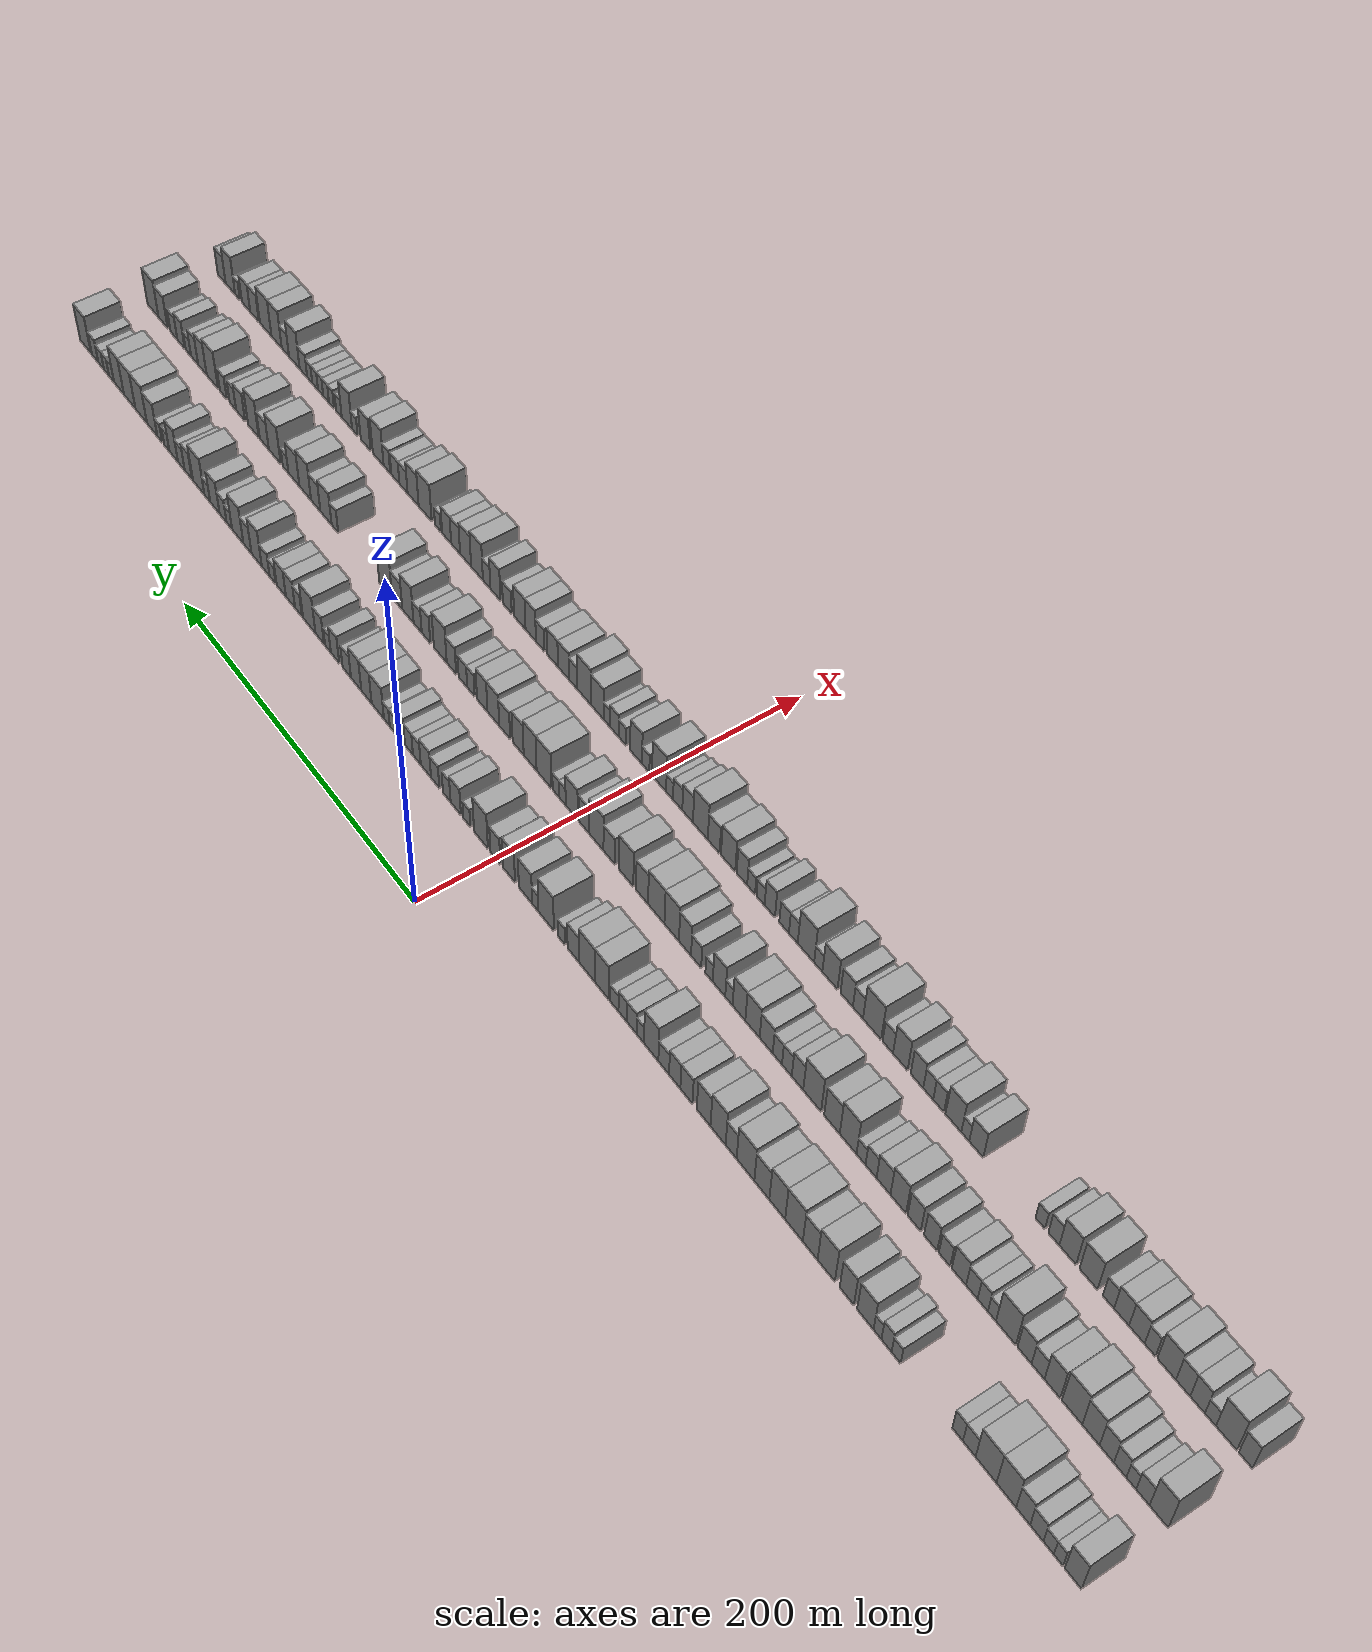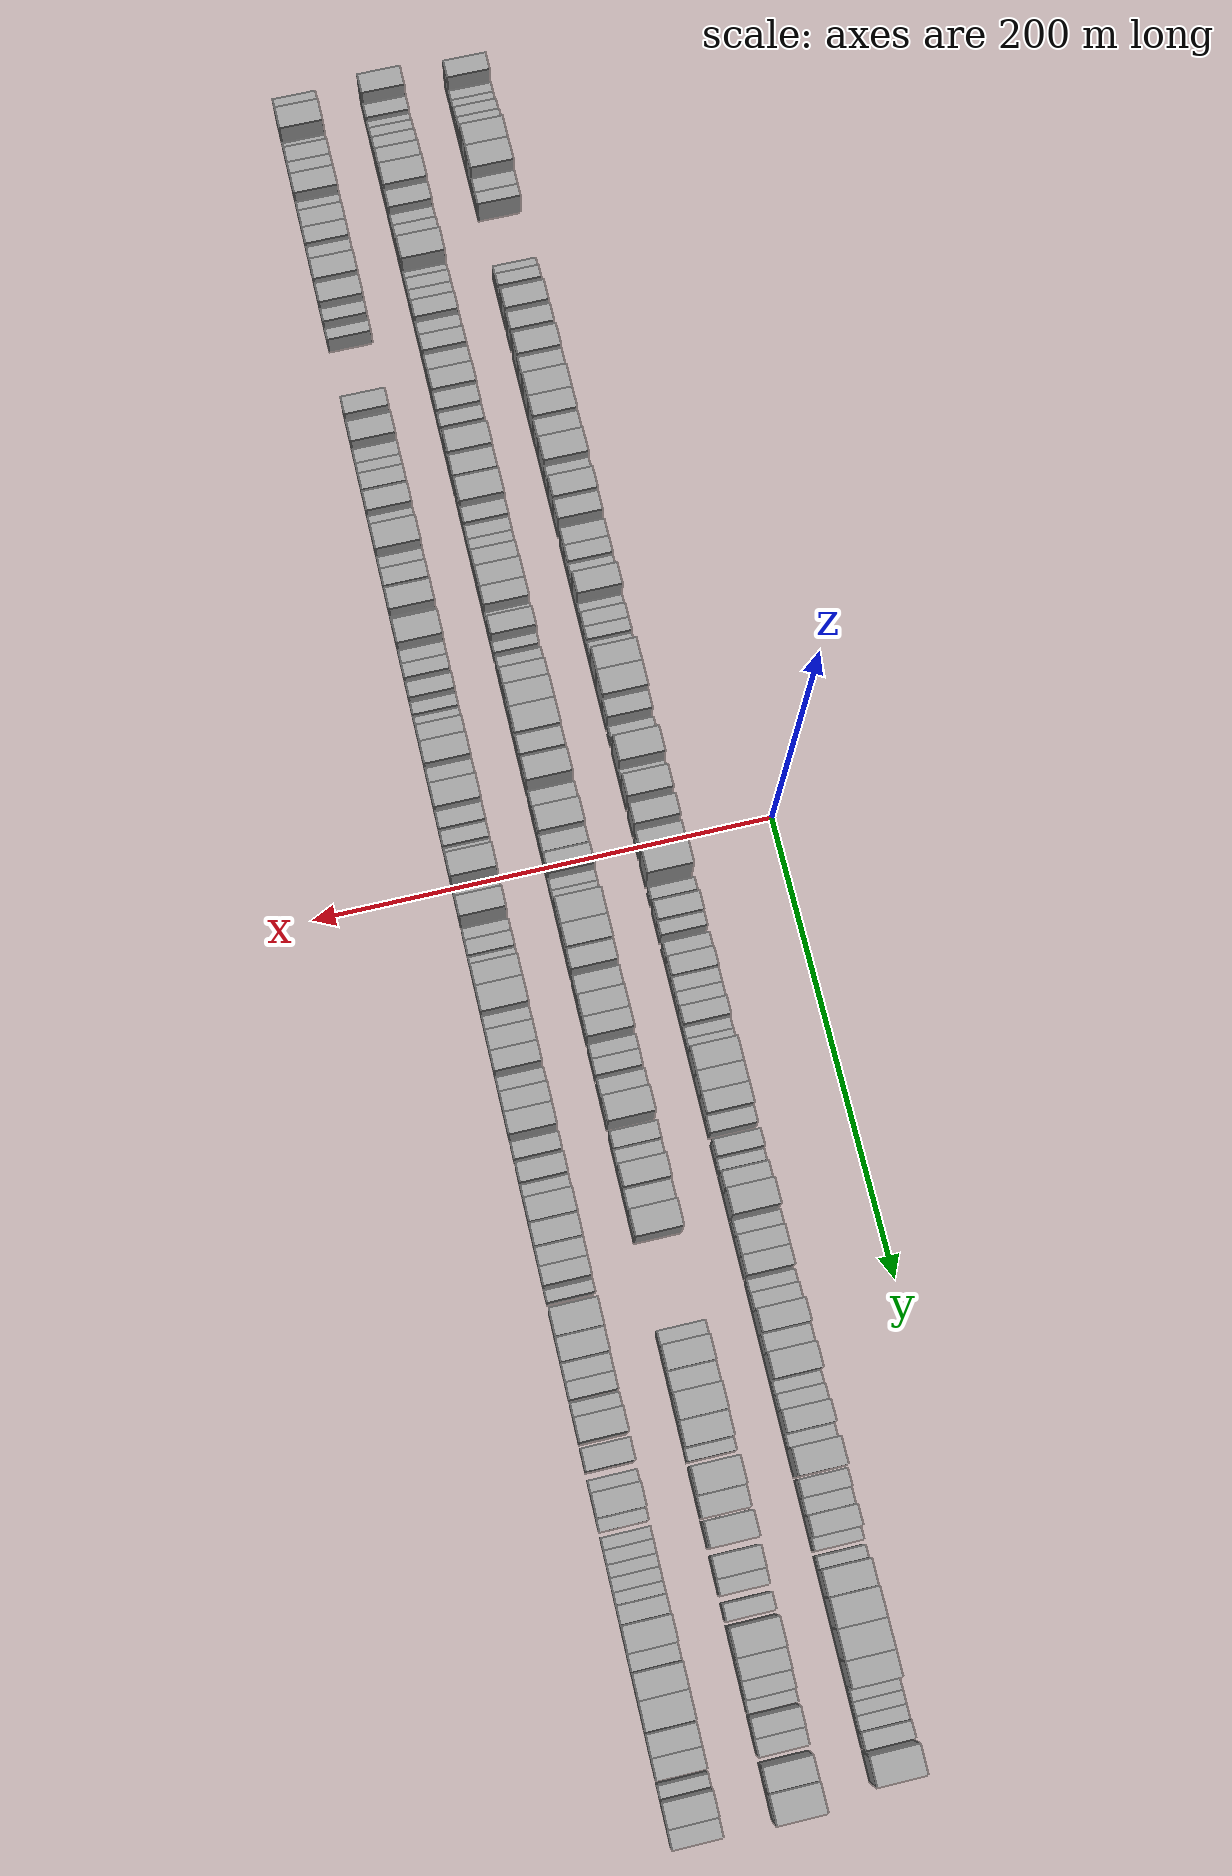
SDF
<sdf version="1.6">
 <world name="default">
  <scene>
   <sky><clouds><speed>12</speed></clouds></sky>
   <ambient>0.4 0.4 0.4 1</ambient>
   <background>0.7 0.7 0.7 1</background>
   <shadows>1</shadows>
  </scene>
  <gravity>0 0 -9.8066</gravity>
  <magnetic_field>6e-06 2.3e-05 -4.2e-05</magnetic_field>
  <physics default="0" name="default_physics" type="ode">
   <ode>
    <solver>
     <type>quick</type>
     <iters>10</iters>
     <sor>1.0</sor>
     <use_dynamic_moi_rescaling>0</use_dynamic_moi_rescaling>
    </solver>
    <constraints>
     <cfm>0</cfm>
     <erp>0.2</erp>
     <contact_max_correcting_vel>100</contact_max_correcting_vel>
     <contact_surface_layer>0.001</contact_surface_layer>
    </constraints>
   </ode>
   <max_step_size>0.004</max_step_size>
   <real_time_factor>1</real_time_factor>
   <real_time_update_rate>250</real_time_update_rate>
  </physics>
  <light name="sun" type="directional">
   <pose>0 0 10 0 0 0</pose>
   <diffuse>0.8 0.8 0.8 1</diffuse>
   <specular>0.2 0.2 0.2 1</specular>
   <attenuation>
    <range>1000</range>
    <constant>0.9</constant>
    <linear>0.01</linear>
    <quadratic>0.001</quadratic>
   </attenuation>
   <direction>-0.5 0.1 -0.9</direction>
  </light>
  <model name="building_1">
   <static>1</static>
   <pose>50.0000 -375.4770 0 0.000000 0.000000 0.000000</pose>
   <link name="link">
    <pose>0 0 10.50 0 0 0</pose>
    <collision name="collision"><geometry><box><size>20.0000 9.0460 21.0000</size></box></geometry></collision>
    <visual name="visual">
     <cast_shadows>0</cast_shadows>
     <geometry><box><size>20.0000 9.0460 21.0000</size></box></geometry>
     <material>
      <script>
       <uri>model://grey_wall/materials/scripts</uri>
       <uri>model://grey_wall/materials/textures</uri>
       <name>vrc/grey_wall</name>
      </script>
     </material>
    </visual>
   </link>
  </model>
  <model name="building_2">
   <static>1</static>
   <pose>50.0000 -367.4467 0 0.000000 0.000000 0.000000</pose>
   <link name="link">
    <pose>0 0 6.00 0 0 0</pose>
    <collision name="collision"><geometry><box><size>20.0000 5.0145 12.0000</size></box></geometry></collision>
    <visual name="visual">
     <cast_shadows>0</cast_shadows>
     <geometry><box><size>20.0000 5.0145 12.0000</size></box></geometry>
     <material>
      <script>
       <uri>model://grey_wall/materials/scripts</uri>
       <uri>model://grey_wall/materials/textures</uri>
       <name>vrc/grey_wall</name>
      </script>
     </material>
    </visual>
   </link>
  </model>
  <model name="building_3">
   <static>1</static>
   <pose>50.0000 -362.0838 0 0.000000 0.000000 0.000000</pose>
   <link name="link">
    <pose>0 0 6.00 0 0 0</pose>
    <collision name="collision"><geometry><box><size>20.0000 5.7114 12.0000</size></box></geometry></collision>
    <visual name="visual">
     <cast_shadows>0</cast_shadows>
     <geometry><box><size>20.0000 5.7114 12.0000</size></box></geometry>
     <material>
      <script>
       <uri>model://grey_wall/materials/scripts</uri>
       <uri>model://grey_wall/materials/textures</uri>
       <name>vrc/grey_wall</name>
      </script>
     </material>
    </visual>
   </link>
  </model>
  <model name="building_4">
   <static>1</static>
   <pose>50.0000 -355.5702 0 0.000000 0.000000 0.000000</pose>
   <link name="link">
    <pose>0 0 7.50 0 0 0</pose>
    <collision name="collision"><geometry><box><size>20.0000 7.3159 15.0000</size></box></geometry></collision>
    <visual name="visual">
     <cast_shadows>0</cast_shadows>
     <geometry><box><size>20.0000 7.3159 15.0000</size></box></geometry>
     <material>
      <script>
       <uri>model://grey_wall/materials/scripts</uri>
       <uri>model://grey_wall/materials/textures</uri>
       <name>vrc/grey_wall</name>
      </script>
     </material>
    </visual>
   </link>
  </model>
  <model name="building_5">
   <static>1</static>
   <pose>50.0000 -348.0500 0 0.000000 0.000000 0.000000</pose>
   <link name="link">
    <pose>0 0 9.00 0 0 0</pose>
    <collision name="collision"><geometry><box><size>20.0000 7.7244 18.0000</size></box></geometry></collision>
    <visual name="visual">
     <cast_shadows>0</cast_shadows>
     <geometry><box><size>20.0000 7.7244 18.0000</size></box></geometry>
     <material>
      <script>
       <uri>model://grey_wall/materials/scripts</uri>
       <uri>model://grey_wall/materials/textures</uri>
       <name>vrc/grey_wall</name>
      </script>
     </material>
    </visual>
   </link>
  </model>
  <model name="building_6">
   <static>1</static>
   <pose>50.0000 -338.6430 0 0.000000 0.000000 0.000000</pose>
   <link name="link">
    <pose>0 0 12.00 0 0 0</pose>
    <collision name="collision"><geometry><box><size>20.0000 11.0895 24.0000</size></box></geometry></collision>
    <visual name="visual">
     <cast_shadows>0</cast_shadows>
     <geometry><box><size>20.0000 11.0895 24.0000</size></box></geometry>
     <material>
      <script>
       <uri>model://grey_wall/materials/scripts</uri>
       <uri>model://grey_wall/materials/textures</uri>
       <name>vrc/grey_wall</name>
      </script>
     </material>
    </visual>
   </link>
  </model>
  <model name="building_7">
   <static>1</static>
   <pose>50.0000 -327.1445 0 0.000000 0.000000 0.000000</pose>
   <link name="link">
    <pose>0 0 12.00 0 0 0</pose>
    <collision name="collision"><geometry><box><size>20.0000 11.9075 24.0000</size></box></geometry></collision>
    <visual name="visual">
     <cast_shadows>0</cast_shadows>
     <geometry><box><size>20.0000 11.9075 24.0000</size></box></geometry>
     <material>
      <script>
       <uri>model://grey_wall/materials/scripts</uri>
       <uri>model://grey_wall/materials/textures</uri>
       <name>vrc/grey_wall</name>
      </script>
     </material>
    </visual>
   </link>
  </model>
  <model name="building_8">
   <static>1</static>
   <pose>50.0000 -317.5365 0 0.000000 0.000000 0.000000</pose>
   <link name="link">
    <pose>0 0 7.50 0 0 0</pose>
    <collision name="collision"><geometry><box><size>20.0000 7.3085 15.0000</size></box></geometry></collision>
    <visual name="visual">
     <cast_shadows>0</cast_shadows>
     <geometry><box><size>20.0000 7.3085 15.0000</size></box></geometry>
     <material>
      <script>
       <uri>model://grey_wall/materials/scripts</uri>
       <uri>model://grey_wall/materials/textures</uri>
       <name>vrc/grey_wall</name>
      </script>
     </material>
    </visual>
   </link>
  </model>
  <model name="building_9">
   <static>1</static>
   <pose>50.0000 -310.8080 0 0.000000 0.000000 0.000000</pose>
   <link name="link">
    <pose>0 0 7.50 0 0 0</pose>
    <collision name="collision"><geometry><box><size>20.0000 6.1485 15.0000</size></box></geometry></collision>
    <visual name="visual">
     <cast_shadows>0</cast_shadows>
     <geometry><box><size>20.0000 6.1485 15.0000</size></box></geometry>
     <material>
      <script>
       <uri>model://grey_wall/materials/scripts</uri>
       <uri>model://grey_wall/materials/textures</uri>
       <name>vrc/grey_wall</name>
      </script>
     </material>
    </visual>
   </link>
  </model>
  <model name="building_10">
   <static>1</static>
   <pose>50.0000 -274.5276 0 0.000000 0.000000 0.000000</pose>
   <link name="link">
    <pose>0 0 6.00 0 0 0</pose>
    <collision name="collision"><geometry><box><size>20.0000 5.4708 12.0000</size></box></geometry></collision>
    <visual name="visual">
     <cast_shadows>0</cast_shadows>
     <geometry><box><size>20.0000 5.4708 12.0000</size></box></geometry>
     <material>
      <script>
       <uri>model://grey_wall/materials/scripts</uri>
       <uri>model://grey_wall/materials/textures</uri>
       <name>vrc/grey_wall</name>
      </script>
     </material>
    </visual>
   </link>
  </model>
  <model name="building_11">
   <static>1</static>
   <pose>50.0000 -268.7220 0 0.000000 0.000000 0.000000</pose>
   <link name="link">
    <pose>0 0 7.50 0 0 0</pose>
    <collision name="collision"><geometry><box><size>20.0000 6.1404 15.0000</size></box></geometry></collision>
    <visual name="visual">
     <cast_shadows>0</cast_shadows>
     <geometry><box><size>20.0000 6.1404 15.0000</size></box></geometry>
     <material>
      <script>
       <uri>model://grey_wall/materials/scripts</uri>
       <uri>model://grey_wall/materials/textures</uri>
       <name>vrc/grey_wall</name>
      </script>
     </material>
    </visual>
   </link>
  </model>
  <model name="building_12">
   <static>1</static>
   <pose>50.0000 -263.2417 0 0.000000 0.000000 0.000000</pose>
   <link name="link">
    <pose>0 0 6.00 0 0 0</pose>
    <collision name="collision"><geometry><box><size>20.0000 4.8203 12.0000</size></box></geometry></collision>
    <visual name="visual">
     <cast_shadows>0</cast_shadows>
     <geometry><box><size>20.0000 4.8203 12.0000</size></box></geometry>
     <material>
      <script>
       <uri>model://grey_wall/materials/scripts</uri>
       <uri>model://grey_wall/materials/textures</uri>
       <name>vrc/grey_wall</name>
      </script>
     </material>
    </visual>
   </link>
  </model>
  <model name="building_13">
   <static>1</static>
   <pose>50.0000 -255.8133 0 0.000000 0.000000 0.000000</pose>
   <link name="link">
    <pose>0 0 10.50 0 0 0</pose>
    <collision name="collision"><geometry><box><size>20.0000 10.0364 21.0000</size></box></geometry></collision>
    <visual name="visual">
     <cast_shadows>0</cast_shadows>
     <geometry><box><size>20.0000 10.0364 21.0000</size></box></geometry>
     <material>
      <script>
       <uri>model://grey_wall/materials/scripts</uri>
       <uri>model://grey_wall/materials/textures</uri>
       <name>vrc/grey_wall</name>
      </script>
     </material>
    </visual>
   </link>
  </model>
  <model name="building_14">
   <static>1</static>
   <pose>50.0000 -244.3939 0 0.000000 0.000000 0.000000</pose>
   <link name="link">
    <pose>0 0 10.50 0 0 0</pose>
    <collision name="collision"><geometry><box><size>20.0000 8.8023 21.0000</size></box></geometry></collision>
    <visual name="visual">
     <cast_shadows>0</cast_shadows>
     <geometry><box><size>20.0000 8.8023 21.0000</size></box></geometry>
     <material>
      <script>
       <uri>model://grey_wall/materials/scripts</uri>
       <uri>model://grey_wall/materials/textures</uri>
       <name>vrc/grey_wall</name>
      </script>
     </material>
    </visual>
   </link>
  </model>
  <model name="building_15">
   <static>1</static>
   <pose>50.0000 -231.5478 0 0.000000 0.000000 0.000000</pose>
   <link name="link">
    <pose>0 0 12.00 0 0 0</pose>
    <collision name="collision"><geometry><box><size>20.0000 10.8899 24.0000</size></box></geometry></collision>
    <visual name="visual">
     <cast_shadows>0</cast_shadows>
     <geometry><box><size>20.0000 10.8899 24.0000</size></box></geometry>
     <material>
      <script>
       <uri>model://grey_wall/materials/scripts</uri>
       <uri>model://grey_wall/materials/textures</uri>
       <name>vrc/grey_wall</name>
      </script>
     </material>
    </visual>
   </link>
  </model>
  <model name="building_16">
   <static>1</static>
   <pose>50.0000 -221.4328 0 0.000000 0.000000 0.000000</pose>
   <link name="link">
    <pose>0 0 10.50 0 0 0</pose>
    <collision name="collision"><geometry><box><size>20.0000 9.3402 21.0000</size></box></geometry></collision>
    <visual name="visual">
     <cast_shadows>0</cast_shadows>
     <geometry><box><size>20.0000 9.3402 21.0000</size></box></geometry>
     <material>
      <script>
       <uri>model://grey_wall/materials/scripts</uri>
       <uri>model://grey_wall/materials/textures</uri>
       <name>vrc/grey_wall</name>
      </script>
     </material>
    </visual>
   </link>
  </model>
  <model name="building_17">
   <static>1</static>
   <pose>50.0000 -211.0755 0 0.000000 0.000000 0.000000</pose>
   <link name="link">
    <pose>0 0 12.00 0 0 0</pose>
    <collision name="collision"><geometry><box><size>20.0000 11.3743 24.0000</size></box></geometry></collision>
    <visual name="visual">
     <cast_shadows>0</cast_shadows>
     <geometry><box><size>20.0000 11.3743 24.0000</size></box></geometry>
     <material>
      <script>
       <uri>model://grey_wall/materials/scripts</uri>
       <uri>model://grey_wall/materials/textures</uri>
       <name>vrc/grey_wall</name>
      </script>
     </material>
    </visual>
   </link>
  </model>
  <model name="building_18">
   <static>1</static>
   <pose>50.0000 -200.2660 0 0.000000 0.000000 0.000000</pose>
   <link name="link">
    <pose>0 0 12.00 0 0 0</pose>
    <collision name="collision"><geometry><box><size>20.0000 10.2447 24.0000</size></box></geometry></collision>
    <visual name="visual">
     <cast_shadows>0</cast_shadows>
     <geometry><box><size>20.0000 10.2447 24.0000</size></box></geometry>
     <material>
      <script>
       <uri>model://grey_wall/materials/scripts</uri>
       <uri>model://grey_wall/materials/textures</uri>
       <name>vrc/grey_wall</name>
      </script>
     </material>
    </visual>
   </link>
  </model>
  <model name="building_19">
   <static>1</static>
   <pose>50.0000 -190.2318 0 0.000000 0.000000 0.000000</pose>
   <link name="link">
    <pose>0 0 10.50 0 0 0</pose>
    <collision name="collision"><geometry><box><size>20.0000 9.8237 21.0000</size></box></geometry></collision>
    <visual name="visual">
     <cast_shadows>0</cast_shadows>
     <geometry><box><size>20.0000 9.8237 21.0000</size></box></geometry>
     <material>
      <script>
       <uri>model://grey_wall/materials/scripts</uri>
       <uri>model://grey_wall/materials/textures</uri>
       <name>vrc/grey_wall</name>
      </script>
     </material>
    </visual>
   </link>
  </model>
  <model name="building_20">
   <static>1</static>
   <pose>50.0000 -179.4663 0 0.000000 0.000000 0.000000</pose>
   <link name="link">
    <pose>0 0 12.00 0 0 0</pose>
    <collision name="collision"><geometry><box><size>20.0000 11.7075 24.0000</size></box></geometry></collision>
    <visual name="visual">
     <cast_shadows>0</cast_shadows>
     <geometry><box><size>20.0000 11.7075 24.0000</size></box></geometry>
     <material>
      <script>
       <uri>model://grey_wall/materials/scripts</uri>
       <uri>model://grey_wall/materials/textures</uri>
       <name>vrc/grey_wall</name>
      </script>
     </material>
    </visual>
   </link>
  </model>
  <model name="building_21">
   <static>1</static>
   <pose>50.0000 -169.9237 0 0.000000 0.000000 0.000000</pose>
   <link name="link">
    <pose>0 0 9.00 0 0 0</pose>
    <collision name="collision"><geometry><box><size>20.0000 7.3776 18.0000</size></box></geometry></collision>
    <visual name="visual">
     <cast_shadows>0</cast_shadows>
     <geometry><box><size>20.0000 7.3776 18.0000</size></box></geometry>
     <material>
      <script>
       <uri>model://grey_wall/materials/scripts</uri>
       <uri>model://grey_wall/materials/textures</uri>
       <name>vrc/grey_wall</name>
      </script>
     </material>
    </visual>
   </link>
  </model>
  <model name="building_22">
   <static>1</static>
   <pose>50.0000 -161.1338 0 0.000000 0.000000 0.000000</pose>
   <link name="link">
    <pose>0 0 12.00 0 0 0</pose>
    <collision name="collision"><geometry><box><size>20.0000 10.2021 24.0000</size></box></geometry></collision>
    <visual name="visual">
     <cast_shadows>0</cast_shadows>
     <geometry><box><size>20.0000 10.2021 24.0000</size></box></geometry>
     <material>
      <script>
       <uri>model://grey_wall/materials/scripts</uri>
       <uri>model://grey_wall/materials/textures</uri>
       <name>vrc/grey_wall</name>
      </script>
     </material>
    </visual>
   </link>
  </model>
  <model name="building_23">
   <static>1</static>
   <pose>50.0000 -151.3745 0 0.000000 0.000000 0.000000</pose>
   <link name="link">
    <pose>0 0 10.50 0 0 0</pose>
    <collision name="collision"><geometry><box><size>20.0000 9.3167 21.0000</size></box></geometry></collision>
    <visual name="visual">
     <cast_shadows>0</cast_shadows>
     <geometry><box><size>20.0000 9.3167 21.0000</size></box></geometry>
     <material>
      <script>
       <uri>model://grey_wall/materials/scripts</uri>
       <uri>model://grey_wall/materials/textures</uri>
       <name>vrc/grey_wall</name>
      </script>
     </material>
    </visual>
   </link>
  </model>
  <model name="building_24">
   <static>1</static>
   <pose>50.0000 -139.5765 0 0.000000 0.000000 0.000000</pose>
   <link name="link">
    <pose>0 0 9.00 0 0 0</pose>
    <collision name="collision"><geometry><box><size>20.0000 8.2792 18.0000</size></box></geometry></collision>
    <visual name="visual">
     <cast_shadows>0</cast_shadows>
     <geometry><box><size>20.0000 8.2792 18.0000</size></box></geometry>
     <material>
      <script>
       <uri>model://grey_wall/materials/scripts</uri>
       <uri>model://grey_wall/materials/textures</uri>
       <name>vrc/grey_wall</name>
      </script>
     </material>
    </visual>
   </link>
  </model>
  <model name="building_25">
   <static>1</static>
   <pose>50.0000 -131.5119 0 0.000000 0.000000 0.000000</pose>
   <link name="link">
    <pose>0 0 9.00 0 0 0</pose>
    <collision name="collision"><geometry><box><size>20.0000 7.8499 18.0000</size></box></geometry></collision>
    <visual name="visual">
     <cast_shadows>0</cast_shadows>
     <geometry><box><size>20.0000 7.8499 18.0000</size></box></geometry>
     <material>
      <script>
       <uri>model://grey_wall/materials/scripts</uri>
       <uri>model://grey_wall/materials/textures</uri>
       <name>vrc/grey_wall</name>
      </script>
     </material>
    </visual>
   </link>
  </model>
  <model name="building_26">
   <static>1</static>
   <pose>50.0000 -123.8515 0 0.000000 0.000000 0.000000</pose>
   <link name="link">
    <pose>0 0 7.50 0 0 0</pose>
    <collision name="collision"><geometry><box><size>20.0000 7.4709 15.0000</size></box></geometry></collision>
    <visual name="visual">
     <cast_shadows>0</cast_shadows>
     <geometry><box><size>20.0000 7.4709 15.0000</size></box></geometry>
     <material>
      <script>
       <uri>model://grey_wall/materials/scripts</uri>
       <uri>model://grey_wall/materials/textures</uri>
       <name>vrc/grey_wall</name>
      </script>
     </material>
    </visual>
   </link>
  </model>
  <model name="building_27">
   <static>1</static>
   <pose>50.0000 -115.0399 0 0.000000 0.000000 0.000000</pose>
   <link name="link">
    <pose>0 0 12.00 0 0 0</pose>
    <collision name="collision"><geometry><box><size>20.0000 10.1523 24.0000</size></box></geometry></collision>
    <visual name="visual">
     <cast_shadows>0</cast_shadows>
     <geometry><box><size>20.0000 10.1523 24.0000</size></box></geometry>
     <material>
      <script>
       <uri>model://grey_wall/materials/scripts</uri>
       <uri>model://grey_wall/materials/textures</uri>
       <name>vrc/grey_wall</name>
      </script>
     </material>
    </visual>
   </link>
  </model>
  <model name="building_28">
   <static>1</static>
   <pose>50.0000 -107.3842 0 0.000000 0.000000 0.000000</pose>
   <link name="link">
    <pose>0 0 6.00 0 0 0</pose>
    <collision name="collision"><geometry><box><size>20.0000 5.1590 12.0000</size></box></geometry></collision>
    <visual name="visual">
     <cast_shadows>0</cast_shadows>
     <geometry><box><size>20.0000 5.1590 12.0000</size></box></geometry>
     <material>
      <script>
       <uri>model://grey_wall/materials/scripts</uri>
       <uri>model://grey_wall/materials/textures</uri>
       <name>vrc/grey_wall</name>
      </script>
     </material>
    </visual>
   </link>
  </model>
  <model name="building_29">
   <static>1</static>
   <pose>50.0000 -101.3561 0 0.000000 0.000000 0.000000</pose>
   <link name="link">
    <pose>0 0 7.50 0 0 0</pose>
    <collision name="collision"><geometry><box><size>20.0000 6.8971 15.0000</size></box></geometry></collision>
    <visual name="visual">
     <cast_shadows>0</cast_shadows>
     <geometry><box><size>20.0000 6.8971 15.0000</size></box></geometry>
     <material>
      <script>
       <uri>model://grey_wall/materials/scripts</uri>
       <uri>model://grey_wall/materials/textures</uri>
       <name>vrc/grey_wall</name>
      </script>
     </material>
    </visual>
   </link>
  </model>
  <model name="building_30">
   <static>1</static>
   <pose>50.0000 -94.8345 0 0.000000 0.000000 0.000000</pose>
   <link name="link">
    <pose>0 0 7.50 0 0 0</pose>
    <collision name="collision"><geometry><box><size>20.0000 6.1461 15.0000</size></box></geometry></collision>
    <visual name="visual">
     <cast_shadows>0</cast_shadows>
     <geometry><box><size>20.0000 6.1461 15.0000</size></box></geometry>
     <material>
      <script>
       <uri>model://grey_wall/materials/scripts</uri>
       <uri>model://grey_wall/materials/textures</uri>
       <name>vrc/grey_wall</name>
      </script>
     </material>
    </visual>
   </link>
  </model>
  <model name="building_31">
   <static>1</static>
   <pose>50.0000 -88.8080 0 0.000000 0.000000 0.000000</pose>
   <link name="link">
    <pose>0 0 6.00 0 0 0</pose>
    <collision name="collision"><geometry><box><size>20.0000 5.9069 12.0000</size></box></geometry></collision>
    <visual name="visual">
     <cast_shadows>0</cast_shadows>
     <geometry><box><size>20.0000 5.9069 12.0000</size></box></geometry>
     <material>
      <script>
       <uri>model://grey_wall/materials/scripts</uri>
       <uri>model://grey_wall/materials/textures</uri>
       <name>vrc/grey_wall</name>
      </script>
     </material>
    </visual>
   </link>
  </model>
  <model name="building_32">
   <static>1</static>
   <pose>50.0000 -79.6111 0 0.000000 0.000000 0.000000</pose>
   <link name="link">
    <pose>0 0 12.00 0 0 0</pose>
    <collision name="collision"><geometry><box><size>20.0000 10.4868 24.0000</size></box></geometry></collision>
    <visual name="visual">
     <cast_shadows>0</cast_shadows>
     <geometry><box><size>20.0000 10.4868 24.0000</size></box></geometry>
     <material>
      <script>
       <uri>model://grey_wall/materials/scripts</uri>
       <uri>model://grey_wall/materials/textures</uri>
       <name>vrc/grey_wall</name>
      </script>
     </material>
    </visual>
   </link>
  </model>
  <model name="building_33">
   <static>1</static>
   <pose>50.0000 -68.5768 0 0.000000 0.000000 0.000000</pose>
   <link name="link">
    <pose>0 0 12.00 0 0 0</pose>
    <collision name="collision"><geometry><box><size>20.0000 11.5819 24.0000</size></box></geometry></collision>
    <visual name="visual">
     <cast_shadows>0</cast_shadows>
     <geometry><box><size>20.0000 11.5819 24.0000</size></box></geometry>
     <material>
      <script>
       <uri>model://grey_wall/materials/scripts</uri>
       <uri>model://grey_wall/materials/textures</uri>
       <name>vrc/grey_wall</name>
      </script>
     </material>
    </visual>
   </link>
  </model>
  <model name="building_34">
   <static>1</static>
   <pose>50.0000 -58.6236 0 0.000000 0.000000 0.000000</pose>
   <link name="link">
    <pose>0 0 9.00 0 0 0</pose>
    <collision name="collision"><geometry><box><size>20.0000 8.3245 18.0000</size></box></geometry></collision>
    <visual name="visual">
     <cast_shadows>0</cast_shadows>
     <geometry><box><size>20.0000 8.3245 18.0000</size></box></geometry>
     <material>
      <script>
       <uri>model://grey_wall/materials/scripts</uri>
       <uri>model://grey_wall/materials/textures</uri>
       <name>vrc/grey_wall</name>
      </script>
     </material>
    </visual>
   </link>
  </model>
  <model name="building_35">
   <static>1</static>
   <pose>50.0000 -49.8125 0 0.000000 0.000000 0.000000</pose>
   <link name="link">
    <pose>0 0 6.00 0 0 0</pose>
    <collision name="collision"><geometry><box><size>20.0000 5.2978 12.0000</size></box></geometry></collision>
    <visual name="visual">
     <cast_shadows>0</cast_shadows>
     <geometry><box><size>20.0000 5.2978 12.0000</size></box></geometry>
     <material>
      <script>
       <uri>model://grey_wall/materials/scripts</uri>
       <uri>model://grey_wall/materials/textures</uri>
       <name>vrc/grey_wall</name>
      </script>
     </material>
    </visual>
   </link>
  </model>
  <model name="building_36">
   <static>1</static>
   <pose>50.0000 -38.3444 0 0.000000 0.000000 0.000000</pose>
   <link name="link">
    <pose>0 0 12.00 0 0 0</pose>
    <collision name="collision"><geometry><box><size>20.0000 11.6383 24.0000</size></box></geometry></collision>
    <visual name="visual">
     <cast_shadows>0</cast_shadows>
     <geometry><box><size>20.0000 11.6383 24.0000</size></box></geometry>
     <material>
      <script>
       <uri>model://grey_wall/materials/scripts</uri>
       <uri>model://grey_wall/materials/textures</uri>
       <name>vrc/grey_wall</name>
      </script>
     </material>
    </visual>
   </link>
  </model>
  <model name="building_37">
   <static>1</static>
   <pose>50.0000 -30.1147 0 0.000000 0.000000 0.000000</pose>
   <link name="link">
    <pose>0 0 6.00 0 0 0</pose>
    <collision name="collision"><geometry><box><size>20.0000 4.8212 12.0000</size></box></geometry></collision>
    <visual name="visual">
     <cast_shadows>0</cast_shadows>
     <geometry><box><size>20.0000 4.8212 12.0000</size></box></geometry>
     <material>
      <script>
       <uri>model://grey_wall/materials/scripts</uri>
       <uri>model://grey_wall/materials/textures</uri>
       <name>vrc/grey_wall</name>
      </script>
     </material>
    </visual>
   </link>
  </model>
  <model name="building_38">
   <static>1</static>
   <pose>50.0000 -22.6148 0 0.000000 0.000000 0.000000</pose>
   <link name="link">
    <pose>0 0 10.50 0 0 0</pose>
    <collision name="collision"><geometry><box><size>20.0000 10.1786 21.0000</size></box></geometry></collision>
    <visual name="visual">
     <cast_shadows>0</cast_shadows>
     <geometry><box><size>20.0000 10.1786 21.0000</size></box></geometry>
     <material>
      <script>
       <uri>model://grey_wall/materials/scripts</uri>
       <uri>model://grey_wall/materials/textures</uri>
       <name>vrc/grey_wall</name>
      </script>
     </material>
    </visual>
   </link>
  </model>
  <model name="building_39">
   <static>1</static>
   <pose>50.0000 -9.8363 0 0.000000 0.000000 0.000000</pose>
   <link name="link">
    <pose>0 0 10.50 0 0 0</pose>
    <collision name="collision"><geometry><box><size>20.0000 9.3783 21.0000</size></box></geometry></collision>
    <visual name="visual">
     <cast_shadows>0</cast_shadows>
     <geometry><box><size>20.0000 9.3783 21.0000</size></box></geometry>
     <material>
      <script>
       <uri>model://grey_wall/materials/scripts</uri>
       <uri>model://grey_wall/materials/textures</uri>
       <name>vrc/grey_wall</name>
      </script>
     </material>
    </visual>
   </link>
  </model>
  <model name="building_40">
   <static>1</static>
   <pose>50.0000 0.7481 0 0.000000 0.000000 0.000000</pose>
   <link name="link">
    <pose>0 0 9.00 0 0 0</pose>
    <collision name="collision"><geometry><box><size>20.0000 7.7905 18.0000</size></box></geometry></collision>
    <visual name="visual">
     <cast_shadows>0</cast_shadows>
     <geometry><box><size>20.0000 7.7905 18.0000</size></box></geometry>
     <material>
      <script>
       <uri>model://grey_wall/materials/scripts</uri>
       <uri>model://grey_wall/materials/textures</uri>
       <name>vrc/grey_wall</name>
      </script>
     </material>
    </visual>
   </link>
  </model>
  <model name="building_41">
   <static>1</static>
   <pose>50.0000 12.1011 0 0.000000 0.000000 0.000000</pose>
   <link name="link">
    <pose>0 0 12.00 0 0 0</pose>
    <collision name="collision"><geometry><box><size>20.0000 10.9155 24.0000</size></box></geometry></collision>
    <visual name="visual">
     <cast_shadows>0</cast_shadows>
     <geometry><box><size>20.0000 10.9155 24.0000</size></box></geometry>
     <material>
      <script>
       <uri>model://grey_wall/materials/scripts</uri>
       <uri>model://grey_wall/materials/textures</uri>
       <name>vrc/grey_wall</name>
      </script>
     </material>
    </visual>
   </link>
  </model>
  <model name="building_42">
   <static>1</static>
   <pose>50.0000 23.3495 0 0.000000 0.000000 0.000000</pose>
   <link name="link">
    <pose>0 0 6.00 0 0 0</pose>
    <collision name="collision"><geometry><box><size>20.0000 5.5812 12.0000</size></box></geometry></collision>
    <visual name="visual">
     <cast_shadows>0</cast_shadows>
     <geometry><box><size>20.0000 5.5812 12.0000</size></box></geometry>
     <material>
      <script>
       <uri>model://grey_wall/materials/scripts</uri>
       <uri>model://grey_wall/materials/textures</uri>
       <name>vrc/grey_wall</name>
      </script>
     </material>
    </visual>
   </link>
  </model>
  <model name="building_43">
   <static>1</static>
   <pose>50.0000 32.3095 0 0.000000 0.000000 0.000000</pose>
   <link name="link">
    <pose>0 0 9.00 0 0 0</pose>
    <collision name="collision"><geometry><box><size>20.0000 8.3389 18.0000</size></box></geometry></collision>
    <visual name="visual">
     <cast_shadows>0</cast_shadows>
     <geometry><box><size>20.0000 8.3389 18.0000</size></box></geometry>
     <material>
      <script>
       <uri>model://grey_wall/materials/scripts</uri>
       <uri>model://grey_wall/materials/textures</uri>
       <name>vrc/grey_wall</name>
      </script>
     </material>
    </visual>
   </link>
  </model>
  <model name="building_44">
   <static>1</static>
   <pose>50.0000 39.5402 0 0.000000 0.000000 0.000000</pose>
   <link name="link">
    <pose>0 0 7.50 0 0 0</pose>
    <collision name="collision"><geometry><box><size>20.0000 6.1225 15.0000</size></box></geometry></collision>
    <visual name="visual">
     <cast_shadows>0</cast_shadows>
     <geometry><box><size>20.0000 6.1225 15.0000</size></box></geometry>
     <material>
      <script>
       <uri>model://grey_wall/materials/scripts</uri>
       <uri>model://grey_wall/materials/textures</uri>
       <name>vrc/grey_wall</name>
      </script>
     </material>
    </visual>
   </link>
  </model>
  <model name="building_45">
   <static>1</static>
   <pose>50.0000 49.0186 0 0.000000 0.000000 0.000000</pose>
   <link name="link">
    <pose>0 0 7.50 0 0 0</pose>
    <collision name="collision"><geometry><box><size>20.0000 6.8342 15.0000</size></box></geometry></collision>
    <visual name="visual">
     <cast_shadows>0</cast_shadows>
     <geometry><box><size>20.0000 6.8342 15.0000</size></box></geometry>
     <material>
      <script>
       <uri>model://grey_wall/materials/scripts</uri>
       <uri>model://grey_wall/materials/textures</uri>
       <name>vrc/grey_wall</name>
      </script>
     </material>
    </visual>
   </link>
  </model>
  <model name="building_46">
   <static>1</static>
   <pose>50.0000 56.6620 0 0.000000 0.000000 0.000000</pose>
   <link name="link">
    <pose>0 0 9.00 0 0 0</pose>
    <collision name="collision"><geometry><box><size>20.0000 8.4526 18.0000</size></box></geometry></collision>
    <visual name="visual">
     <cast_shadows>0</cast_shadows>
     <geometry><box><size>20.0000 8.4526 18.0000</size></box></geometry>
     <material>
      <script>
       <uri>model://grey_wall/materials/scripts</uri>
       <uri>model://grey_wall/materials/textures</uri>
       <name>vrc/grey_wall</name>
      </script>
     </material>
    </visual>
   </link>
  </model>
  <model name="building_47">
   <static>1</static>
   <pose>50.0000 64.1325 0 0.000000 0.000000 0.000000</pose>
   <link name="link">
    <pose>0 0 7.50 0 0 0</pose>
    <collision name="collision"><geometry><box><size>20.0000 6.4883 15.0000</size></box></geometry></collision>
    <visual name="visual">
     <cast_shadows>0</cast_shadows>
     <geometry><box><size>20.0000 6.4883 15.0000</size></box></geometry>
     <material>
      <script>
       <uri>model://grey_wall/materials/scripts</uri>
       <uri>model://grey_wall/materials/textures</uri>
       <name>vrc/grey_wall</name>
      </script>
     </material>
    </visual>
   </link>
  </model>
  <model name="building_48">
   <static>1</static>
   <pose>50.0000 70.6933 0 0.000000 0.000000 0.000000</pose>
   <link name="link">
    <pose>0 0 7.50 0 0 0</pose>
    <collision name="collision"><geometry><box><size>20.0000 6.6332 15.0000</size></box></geometry></collision>
    <visual name="visual">
     <cast_shadows>0</cast_shadows>
     <geometry><box><size>20.0000 6.6332 15.0000</size></box></geometry>
     <material>
      <script>
       <uri>model://grey_wall/materials/scripts</uri>
       <uri>model://grey_wall/materials/textures</uri>
       <name>vrc/grey_wall</name>
      </script>
     </material>
    </visual>
   </link>
  </model>
  <model name="building_49">
   <static>1</static>
   <pose>50.0000 77.9368 0 0.000000 0.000000 0.000000</pose>
   <link name="link">
    <pose>0 0 9.00 0 0 0</pose>
    <collision name="collision"><geometry><box><size>20.0000 7.8539 18.0000</size></box></geometry></collision>
    <visual name="visual">
     <cast_shadows>0</cast_shadows>
     <geometry><box><size>20.0000 7.8539 18.0000</size></box></geometry>
     <material>
      <script>
       <uri>model://grey_wall/materials/scripts</uri>
       <uri>model://grey_wall/materials/textures</uri>
       <name>vrc/grey_wall</name>
      </script>
     </material>
    </visual>
   </link>
  </model>
  <model name="building_50">
   <static>1</static>
   <pose>50.0000 84.3722 0 0.000000 0.000000 0.000000</pose>
   <link name="link">
    <pose>0 0 6.00 0 0 0</pose>
    <collision name="collision"><geometry><box><size>20.0000 5.0170 12.0000</size></box></geometry></collision>
    <visual name="visual">
     <cast_shadows>0</cast_shadows>
     <geometry><box><size>20.0000 5.0170 12.0000</size></box></geometry>
     <material>
      <script>
       <uri>model://grey_wall/materials/scripts</uri>
       <uri>model://grey_wall/materials/textures</uri>
       <name>vrc/grey_wall</name>
      </script>
     </material>
    </visual>
   </link>
  </model>
  <model name="building_51">
   <static>1</static>
   <pose>50.0000 89.3582 0 0.000000 0.000000 0.000000</pose>
   <link name="link">
    <pose>0 0 6.00 0 0 0</pose>
    <collision name="collision"><geometry><box><size>20.0000 4.9549 12.0000</size></box></geometry></collision>
    <visual name="visual">
     <cast_shadows>0</cast_shadows>
     <geometry><box><size>20.0000 4.9549 12.0000</size></box></geometry>
     <material>
      <script>
       <uri>model://grey_wall/materials/scripts</uri>
       <uri>model://grey_wall/materials/textures</uri>
       <name>vrc/grey_wall</name>
      </script>
     </material>
    </visual>
   </link>
  </model>
  <model name="building_52">
   <static>1</static>
   <pose>50.0000 97.0628 0 0.000000 0.000000 0.000000</pose>
   <link name="link">
    <pose>0 0 10.50 0 0 0</pose>
    <collision name="collision"><geometry><box><size>20.0000 10.4544 21.0000</size></box></geometry></collision>
    <visual name="visual">
     <cast_shadows>0</cast_shadows>
     <geometry><box><size>20.0000 10.4544 21.0000</size></box></geometry>
     <material>
      <script>
       <uri>model://grey_wall/materials/scripts</uri>
       <uri>model://grey_wall/materials/textures</uri>
       <name>vrc/grey_wall</name>
      </script>
     </material>
    </visual>
   </link>
  </model>
  <model name="building_53">
   <static>1</static>
   <pose>50.0000 106.7404 0 0.000000 0.000000 0.000000</pose>
   <link name="link">
    <pose>0 0 10.50 0 0 0</pose>
    <collision name="collision"><geometry><box><size>20.0000 8.9007 21.0000</size></box></geometry></collision>
    <visual name="visual">
     <cast_shadows>0</cast_shadows>
     <geometry><box><size>20.0000 8.9007 21.0000</size></box></geometry>
     <material>
      <script>
       <uri>model://grey_wall/materials/scripts</uri>
       <uri>model://grey_wall/materials/textures</uri>
       <name>vrc/grey_wall</name>
      </script>
     </material>
    </visual>
   </link>
  </model>
  <model name="building_54">
   <static>1</static>
   <pose>50.0000 115.7202 0 0.000000 0.000000 0.000000</pose>
   <link name="link">
    <pose>0 0 10.50 0 0 0</pose>
    <collision name="collision"><geometry><box><size>20.0000 9.0589 21.0000</size></box></geometry></collision>
    <visual name="visual">
     <cast_shadows>0</cast_shadows>
     <geometry><box><size>20.0000 9.0589 21.0000</size></box></geometry>
     <material>
      <script>
       <uri>model://grey_wall/materials/scripts</uri>
       <uri>model://grey_wall/materials/textures</uri>
       <name>vrc/grey_wall</name>
      </script>
     </material>
    </visual>
   </link>
  </model>
  <model name="building_55">
   <static>1</static>
   <pose>50.0000 123.8697 0 0.000000 0.000000 0.000000</pose>
   <link name="link">
    <pose>0 0 7.50 0 0 0</pose>
    <collision name="collision"><geometry><box><size>20.0000 7.2401 15.0000</size></box></geometry></collision>
    <visual name="visual">
     <cast_shadows>0</cast_shadows>
     <geometry><box><size>20.0000 7.2401 15.0000</size></box></geometry>
     <material>
      <script>
       <uri>model://grey_wall/materials/scripts</uri>
       <uri>model://grey_wall/materials/textures</uri>
       <name>vrc/grey_wall</name>
      </script>
     </material>
    </visual>
   </link>
  </model>
  <model name="building_56">
   <static>1</static>
   <pose>50.0000 134.1823 0 0.000000 0.000000 0.000000</pose>
   <link name="link">
    <pose>0 0 9.00 0 0 0</pose>
    <collision name="collision"><geometry><box><size>20.0000 7.3850 18.0000</size></box></geometry></collision>
    <visual name="visual">
     <cast_shadows>0</cast_shadows>
     <geometry><box><size>20.0000 7.3850 18.0000</size></box></geometry>
     <material>
      <script>
       <uri>model://grey_wall/materials/scripts</uri>
       <uri>model://grey_wall/materials/textures</uri>
       <name>vrc/grey_wall</name>
      </script>
     </material>
    </visual>
   </link>
  </model>
  <model name="building_57">
   <static>1</static>
   <pose>50.0000 140.3996 0 0.000000 0.000000 0.000000</pose>
   <link name="link">
    <pose>0 0 6.00 0 0 0</pose>
    <collision name="collision"><geometry><box><size>20.0000 5.0495 12.0000</size></box></geometry></collision>
    <visual name="visual">
     <cast_shadows>0</cast_shadows>
     <geometry><box><size>20.0000 5.0495 12.0000</size></box></geometry>
     <material>
      <script>
       <uri>model://grey_wall/materials/scripts</uri>
       <uri>model://grey_wall/materials/textures</uri>
       <name>vrc/grey_wall</name>
      </script>
     </material>
    </visual>
   </link>
  </model>
  <model name="building_58">
   <static>1</static>
   <pose>50.0000 147.7551 0 0.000000 0.000000 0.000000</pose>
   <link name="link">
    <pose>0 0 9.00 0 0 0</pose>
    <collision name="collision"><geometry><box><size>20.0000 7.6616 18.0000</size></box></geometry></collision>
    <visual name="visual">
     <cast_shadows>0</cast_shadows>
     <geometry><box><size>20.0000 7.6616 18.0000</size></box></geometry>
     <material>
      <script>
       <uri>model://grey_wall/materials/scripts</uri>
       <uri>model://grey_wall/materials/textures</uri>
       <name>vrc/grey_wall</name>
      </script>
     </material>
    </visual>
   </link>
  </model>
  <model name="building_59">
   <static>1</static>
   <pose>50.0000 157.1529 0 0.000000 0.000000 0.000000</pose>
   <link name="link">
    <pose>0 0 12.00 0 0 0</pose>
    <collision name="collision"><geometry><box><size>20.0000 11.1340 24.0000</size></box></geometry></collision>
    <visual name="visual">
     <cast_shadows>0</cast_shadows>
     <geometry><box><size>20.0000 11.1340 24.0000</size></box></geometry>
     <material>
      <script>
       <uri>model://grey_wall/materials/scripts</uri>
       <uri>model://grey_wall/materials/textures</uri>
       <name>vrc/grey_wall</name>
      </script>
     </material>
    </visual>
   </link>
  </model>
  <model name="building_60">
   <static>1</static>
   <pose>50.0000 166.8681 0 0.000000 0.000000 0.000000</pose>
   <link name="link">
    <pose>0 0 7.50 0 0 0</pose>
    <collision name="collision"><geometry><box><size>20.0000 6.2963 15.0000</size></box></geometry></collision>
    <visual name="visual">
     <cast_shadows>0</cast_shadows>
     <geometry><box><size>20.0000 6.2963 15.0000</size></box></geometry>
     <material>
      <script>
       <uri>model://grey_wall/materials/scripts</uri>
       <uri>model://grey_wall/materials/textures</uri>
       <name>vrc/grey_wall</name>
      </script>
     </material>
    </visual>
   </link>
  </model>
  <model name="building_61">
   <static>1</static>
   <pose>50.0000 174.1851 0 0.000000 0.000000 0.000000</pose>
   <link name="link">
    <pose>0 0 9.00 0 0 0</pose>
    <collision name="collision"><geometry><box><size>20.0000 8.3378 18.0000</size></box></geometry></collision>
    <visual name="visual">
     <cast_shadows>0</cast_shadows>
     <geometry><box><size>20.0000 8.3378 18.0000</size></box></geometry>
     <material>
      <script>
       <uri>model://grey_wall/materials/scripts</uri>
       <uri>model://grey_wall/materials/textures</uri>
       <name>vrc/grey_wall</name>
      </script>
     </material>
    </visual>
   </link>
  </model>
  <model name="building_62">
   <static>1</static>
   <pose>50.0000 182.5561 0 0.000000 0.000000 0.000000</pose>
   <link name="link">
    <pose>0 0 9.00 0 0 0</pose>
    <collision name="collision"><geometry><box><size>20.0000 8.4043 18.0000</size></box></geometry></collision>
    <visual name="visual">
     <cast_shadows>0</cast_shadows>
     <geometry><box><size>20.0000 8.4043 18.0000</size></box></geometry>
     <material>
      <script>
       <uri>model://grey_wall/materials/scripts</uri>
       <uri>model://grey_wall/materials/textures</uri>
       <name>vrc/grey_wall</name>
      </script>
     </material>
    </visual>
   </link>
  </model>
  <model name="building_63">
   <static>1</static>
   <pose>50.0000 190.5556 0 0.000000 0.000000 0.000000</pose>
   <link name="link">
    <pose>0 0 6.00 0 0 0</pose>
    <collision name="collision"><geometry><box><size>20.0000 5.5946 12.0000</size></box></geometry></collision>
    <visual name="visual">
     <cast_shadows>0</cast_shadows>
     <geometry><box><size>20.0000 5.5946 12.0000</size></box></geometry>
     <material>
      <script>
       <uri>model://grey_wall/materials/scripts</uri>
       <uri>model://grey_wall/materials/textures</uri>
       <name>vrc/grey_wall</name>
      </script>
     </material>
    </visual>
   </link>
  </model>
  <model name="building_64">
   <static>1</static>
   <pose>50.0000 196.9684 0 0.000000 0.000000 0.000000</pose>
   <link name="link">
    <pose>0 0 7.50 0 0 0</pose>
    <collision name="collision"><geometry><box><size>20.0000 7.2310 15.0000</size></box></geometry></collision>
    <visual name="visual">
     <cast_shadows>0</cast_shadows>
     <geometry><box><size>20.0000 7.2310 15.0000</size></box></geometry>
     <material>
      <script>
       <uri>model://grey_wall/materials/scripts</uri>
       <uri>model://grey_wall/materials/textures</uri>
       <name>vrc/grey_wall</name>
      </script>
     </material>
    </visual>
   </link>
  </model>
  <model name="building_65">
   <static>1</static>
   <pose>50.0000 205.4132 0 0.000000 0.000000 0.000000</pose>
   <link name="link">
    <pose>0 0 12.00 0 0 0</pose>
    <collision name="collision"><geometry><box><size>20.0000 9.6585 24.0000</size></box></geometry></collision>
    <visual name="visual">
     <cast_shadows>0</cast_shadows>
     <geometry><box><size>20.0000 9.6585 24.0000</size></box></geometry>
     <material>
      <script>
       <uri>model://grey_wall/materials/scripts</uri>
       <uri>model://grey_wall/materials/textures</uri>
       <name>vrc/grey_wall</name>
      </script>
     </material>
    </visual>
   </link>
  </model>
  <model name="building_66">
   <static>1</static>
   <pose>50.0000 214.0781 0 0.000000 0.000000 0.000000</pose>
   <link name="link">
    <pose>0 0 9.00 0 0 0</pose>
    <collision name="collision"><geometry><box><size>20.0000 7.6714 18.0000</size></box></geometry></collision>
    <visual name="visual">
     <cast_shadows>0</cast_shadows>
     <geometry><box><size>20.0000 7.6714 18.0000</size></box></geometry>
     <material>
      <script>
       <uri>model://grey_wall/materials/scripts</uri>
       <uri>model://grey_wall/materials/textures</uri>
       <name>vrc/grey_wall</name>
      </script>
     </material>
    </visual>
   </link>
  </model>
  <model name="building_67">
   <static>1</static>
   <pose>50.0000 223.2891 0 0.000000 0.000000 0.000000</pose>
   <link name="link">
    <pose>0 0 12.00 0 0 0</pose>
    <collision name="collision"><geometry><box><size>20.0000 10.7506 24.0000</size></box></geometry></collision>
    <visual name="visual">
     <cast_shadows>0</cast_shadows>
     <geometry><box><size>20.0000 10.7506 24.0000</size></box></geometry>
     <material>
      <script>
       <uri>model://grey_wall/materials/scripts</uri>
       <uri>model://grey_wall/materials/textures</uri>
       <name>vrc/grey_wall</name>
      </script>
     </material>
    </visual>
   </link>
  </model>
  <model name="building_68">
   <static>1</static>
   <pose>50.0000 231.3365 0 0.000000 0.000000 0.000000</pose>
   <link name="link">
    <pose>0 0 6.00 0 0 0</pose>
    <collision name="collision"><geometry><box><size>20.0000 5.3441 12.0000</size></box></geometry></collision>
    <visual name="visual">
     <cast_shadows>0</cast_shadows>
     <geometry><box><size>20.0000 5.3441 12.0000</size></box></geometry>
     <material>
      <script>
       <uri>model://grey_wall/materials/scripts</uri>
       <uri>model://grey_wall/materials/textures</uri>
       <name>vrc/grey_wall</name>
      </script>
     </material>
    </visual>
   </link>
  </model>
  <model name="building_69">
   <static>1</static>
   <pose>50.0000 237.3192 0 0.000000 0.000000 0.000000</pose>
   <link name="link">
    <pose>0 0 7.50 0 0 0</pose>
    <collision name="collision"><geometry><box><size>20.0000 6.6214 15.0000</size></box></geometry></collision>
    <visual name="visual">
     <cast_shadows>0</cast_shadows>
     <geometry><box><size>20.0000 6.6214 15.0000</size></box></geometry>
     <material>
      <script>
       <uri>model://grey_wall/materials/scripts</uri>
       <uri>model://grey_wall/materials/textures</uri>
       <name>vrc/grey_wall</name>
      </script>
     </material>
    </visual>
   </link>
  </model>
  <model name="building_70">
   <static>1</static>
   <pose>50.0000 245.1917 0 0.000000 0.000000 0.000000</pose>
   <link name="link">
    <pose>0 0 10.50 0 0 0</pose>
    <collision name="collision"><geometry><box><size>20.0000 9.1236 21.0000</size></box></geometry></collision>
    <visual name="visual">
     <cast_shadows>0</cast_shadows>
     <geometry><box><size>20.0000 9.1236 21.0000</size></box></geometry>
     <material>
      <script>
       <uri>model://grey_wall/materials/scripts</uri>
       <uri>model://grey_wall/materials/textures</uri>
       <name>vrc/grey_wall</name>
      </script>
     </material>
    </visual>
   </link>
  </model>
  <model name="building_71">
   <static>1</static>
   <pose>50.0000 252.5566 0 0.000000 0.000000 0.000000</pose>
   <link name="link">
    <pose>0 0 6.00 0 0 0</pose>
    <collision name="collision"><geometry><box><size>20.0000 5.6062 12.0000</size></box></geometry></collision>
    <visual name="visual">
     <cast_shadows>0</cast_shadows>
     <geometry><box><size>20.0000 5.6062 12.0000</size></box></geometry>
     <material>
      <script>
       <uri>model://grey_wall/materials/scripts</uri>
       <uri>model://grey_wall/materials/textures</uri>
       <name>vrc/grey_wall</name>
      </script>
     </material>
    </visual>
   </link>
  </model>
  <model name="building_72">
   <static>1</static>
   <pose>50.0000 260.9833 0 0.000000 0.000000 0.000000</pose>
   <link name="link">
    <pose>0 0 12.00 0 0 0</pose>
    <collision name="collision"><geometry><box><size>20.0000 11.2474 24.0000</size></box></geometry></collision>
    <visual name="visual">
     <cast_shadows>0</cast_shadows>
     <geometry><box><size>20.0000 11.2474 24.0000</size></box></geometry>
     <material>
      <script>
       <uri>model://grey_wall/materials/scripts</uri>
       <uri>model://grey_wall/materials/textures</uri>
       <name>vrc/grey_wall</name>
      </script>
     </material>
    </visual>
   </link>
  </model>
  <model name="building_73">
   <static>1</static>
   <pose>50.0000 271.2235 0 0.000000 0.000000 0.000000</pose>
   <link name="link">
    <pose>0 0 9.00 0 0 0</pose>
    <collision name="collision"><geometry><box><size>20.0000 7.2329 18.0000</size></box></geometry></collision>
    <visual name="visual">
     <cast_shadows>0</cast_shadows>
     <geometry><box><size>20.0000 7.2329 18.0000</size></box></geometry>
     <material>
      <script>
       <uri>model://grey_wall/materials/scripts</uri>
       <uri>model://grey_wall/materials/textures</uri>
       <name>vrc/grey_wall</name>
      </script>
     </material>
    </visual>
   </link>
  </model>
  <model name="building_74">
   <static>1</static>
   <pose>50.0000 278.1949 0 0.000000 0.000000 0.000000</pose>
   <link name="link">
    <pose>0 0 7.50 0 0 0</pose>
    <collision name="collision"><geometry><box><size>20.0000 6.7098 15.0000</size></box></geometry></collision>
    <visual name="visual">
     <cast_shadows>0</cast_shadows>
     <geometry><box><size>20.0000 6.7098 15.0000</size></box></geometry>
     <material>
      <script>
       <uri>model://grey_wall/materials/scripts</uri>
       <uri>model://grey_wall/materials/textures</uri>
       <name>vrc/grey_wall</name>
      </script>
     </material>
    </visual>
   </link>
  </model>
  <model name="building_75">
   <static>1</static>
   <pose>50.0000 285.7951 0 0.000000 0.000000 0.000000</pose>
   <link name="link">
    <pose>0 0 10.50 0 0 0</pose>
    <collision name="collision"><geometry><box><size>20.0000 8.4907 21.0000</size></box></geometry></collision>
    <visual name="visual">
     <cast_shadows>0</cast_shadows>
     <geometry><box><size>20.0000 8.4907 21.0000</size></box></geometry>
     <material>
      <script>
       <uri>model://grey_wall/materials/scripts</uri>
       <uri>model://grey_wall/materials/textures</uri>
       <name>vrc/grey_wall</name>
      </script>
     </material>
    </visual>
   </link>
  </model>
  <model name="building_76">
   <static>1</static>
   <pose>50.0000 292.6729 0 0.000000 0.000000 0.000000</pose>
   <link name="link">
    <pose>0 0 6.00 0 0 0</pose>
    <collision name="collision"><geometry><box><size>20.0000 5.2649 12.0000</size></box></geometry></collision>
    <visual name="visual">
     <cast_shadows>0</cast_shadows>
     <geometry><box><size>20.0000 5.2649 12.0000</size></box></geometry>
     <material>
      <script>
       <uri>model://grey_wall/materials/scripts</uri>
       <uri>model://grey_wall/materials/textures</uri>
       <name>vrc/grey_wall</name>
      </script>
     </material>
    </visual>
   </link>
  </model>
  <model name="building_77">
   <static>1</static>
   <pose>50.0000 299.8069 0 0.000000 0.000000 0.000000</pose>
   <link name="link">
    <pose>0 0 6.00 0 0 0</pose>
    <collision name="collision"><geometry><box><size>20.0000 5.0031 12.0000</size></box></geometry></collision>
    <visual name="visual">
     <cast_shadows>0</cast_shadows>
     <geometry><box><size>20.0000 5.0031 12.0000</size></box></geometry>
     <material>
      <script>
       <uri>model://grey_wall/materials/scripts</uri>
       <uri>model://grey_wall/materials/textures</uri>
       <name>vrc/grey_wall</name>
      </script>
     </material>
    </visual>
   </link>
  </model>
  <model name="building_78">
   <static>1</static>
   <pose>50.0000 307.5530 0 0.000000 0.000000 0.000000</pose>
   <link name="link">
    <pose>0 0 10.50 0 0 0</pose>
    <collision name="collision"><geometry><box><size>20.0000 10.4891 21.0000</size></box></geometry></collision>
    <visual name="visual">
     <cast_shadows>0</cast_shadows>
     <geometry><box><size>20.0000 10.4891 21.0000</size></box></geometry>
     <material>
      <script>
       <uri>model://grey_wall/materials/scripts</uri>
       <uri>model://grey_wall/materials/textures</uri>
       <name>vrc/grey_wall</name>
      </script>
     </material>
    </visual>
   </link>
  </model>
  <model name="building_79">
   <static>1</static>
   <pose>50.0000 318.7079 0 0.000000 0.000000 0.000000</pose>
   <link name="link">
    <pose>0 0 12.00 0 0 0</pose>
    <collision name="collision"><geometry><box><size>20.0000 11.8206 24.0000</size></box></geometry></collision>
    <visual name="visual">
     <cast_shadows>0</cast_shadows>
     <geometry><box><size>20.0000 11.8206 24.0000</size></box></geometry>
     <material>
      <script>
       <uri>model://grey_wall/materials/scripts</uri>
       <uri>model://grey_wall/materials/textures</uri>
       <name>vrc/grey_wall</name>
      </script>
     </material>
    </visual>
   </link>
  </model>
  <model name="building_80">
   <static>1</static>
   <pose>50.0000 330.6133 0 0.000000 0.000000 0.000000</pose>
   <link name="link">
    <pose>0 0 12.00 0 0 0</pose>
    <collision name="collision"><geometry><box><size>20.0000 11.9901 24.0000</size></box></geometry></collision>
    <visual name="visual">
     <cast_shadows>0</cast_shadows>
     <geometry><box><size>20.0000 11.9901 24.0000</size></box></geometry>
     <material>
      <script>
       <uri>model://grey_wall/materials/scripts</uri>
       <uri>model://grey_wall/materials/textures</uri>
       <name>vrc/grey_wall</name>
      </script>
     </material>
    </visual>
   </link>
  </model>
  <model name="building_81">
   <static>1</static>
   <pose>50.0000 341.7887 0 0.000000 0.000000 0.000000</pose>
   <link name="link">
    <pose>0 0 12.00 0 0 0</pose>
    <collision name="collision"><geometry><box><size>20.0000 10.3607 24.0000</size></box></geometry></collision>
    <visual name="visual">
     <cast_shadows>0</cast_shadows>
     <geometry><box><size>20.0000 10.3607 24.0000</size></box></geometry>
     <material>
      <script>
       <uri>model://grey_wall/materials/scripts</uri>
       <uri>model://grey_wall/materials/textures</uri>
       <name>vrc/grey_wall</name>
      </script>
     </material>
    </visual>
   </link>
  </model>
  <model name="building_82">
   <static>1</static>
   <pose>50.0000 349.6413 0 0.000000 0.000000 0.000000</pose>
   <link name="link">
    <pose>0 0 6.00 0 0 0</pose>
    <collision name="collision"><geometry><box><size>20.0000 5.3445 12.0000</size></box></geometry></collision>
    <visual name="visual">
     <cast_shadows>0</cast_shadows>
     <geometry><box><size>20.0000 5.3445 12.0000</size></box></geometry>
     <material>
      <script>
       <uri>model://grey_wall/materials/scripts</uri>
       <uri>model://grey_wall/materials/textures</uri>
       <name>vrc/grey_wall</name>
      </script>
     </material>
    </visual>
   </link>
  </model>
  <model name="building_83">
   <static>1</static>
   <pose>50.0000 354.9262 0 0.000000 0.000000 0.000000</pose>
   <link name="link">
    <pose>0 0 6.00 0 0 0</pose>
    <collision name="collision"><geometry><box><size>20.0000 5.2252 12.0000</size></box></geometry></collision>
    <visual name="visual">
     <cast_shadows>0</cast_shadows>
     <geometry><box><size>20.0000 5.2252 12.0000</size></box></geometry>
     <material>
      <script>
       <uri>model://grey_wall/materials/scripts</uri>
       <uri>model://grey_wall/materials/textures</uri>
       <name>vrc/grey_wall</name>
      </script>
     </material>
    </visual>
   </link>
  </model>
  <model name="building_84">
   <static>1</static>
   <pose>50.0000 360.4832 0 0.000000 0.000000 0.000000</pose>
   <link name="link">
    <pose>0 0 6.00 0 0 0</pose>
    <collision name="collision"><geometry><box><size>20.0000 5.8889 12.0000</size></box></geometry></collision>
    <visual name="visual">
     <cast_shadows>0</cast_shadows>
     <geometry><box><size>20.0000 5.8889 12.0000</size></box></geometry>
     <material>
      <script>
       <uri>model://grey_wall/materials/scripts</uri>
       <uri>model://grey_wall/materials/textures</uri>
       <name>vrc/grey_wall</name>
      </script>
     </material>
    </visual>
   </link>
  </model>
  <model name="building_85">
   <static>1</static>
   <pose>50.0000 366.8766 0 0.000000 0.000000 0.000000</pose>
   <link name="link">
    <pose>0 0 7.50 0 0 0</pose>
    <collision name="collision"><geometry><box><size>20.0000 6.8979 15.0000</size></box></geometry></collision>
    <visual name="visual">
     <cast_shadows>0</cast_shadows>
     <geometry><box><size>20.0000 6.8979 15.0000</size></box></geometry>
     <material>
      <script>
       <uri>model://grey_wall/materials/scripts</uri>
       <uri>model://grey_wall/materials/textures</uri>
       <name>vrc/grey_wall</name>
      </script>
     </material>
    </visual>
   </link>
  </model>
  <model name="building_86">
   <static>1</static>
   <pose>50.0000 377.1571 0 0.000000 0.000000 0.000000</pose>
   <link name="link">
    <pose>0 0 12.00 0 0 0</pose>
    <collision name="collision"><geometry><box><size>20.0000 11.6630 24.0000</size></box></geometry></collision>
    <visual name="visual">
     <cast_shadows>0</cast_shadows>
     <geometry><box><size>20.0000 11.6630 24.0000</size></box></geometry>
     <material>
      <script>
       <uri>model://grey_wall/materials/scripts</uri>
       <uri>model://grey_wall/materials/textures</uri>
       <name>vrc/grey_wall</name>
      </script>
     </material>
    </visual>
   </link>
  </model>
  <model name="building_87">
   <static>1</static>
   <pose>90.0000 -374.9707 0 0.000000 0.000000 0.000000</pose>
   <link name="link">
    <pose>0 0 12.00 0 0 0</pose>
    <collision name="collision"><geometry><box><size>20.0000 10.0586 24.0000</size></box></geometry></collision>
    <visual name="visual">
     <cast_shadows>0</cast_shadows>
     <geometry><box><size>20.0000 10.0586 24.0000</size></box></geometry>
     <material>
      <script>
       <uri>model://grey_wall/materials/scripts</uri>
       <uri>model://grey_wall/materials/textures</uri>
       <name>vrc/grey_wall</name>
      </script>
     </material>
    </visual>
   </link>
  </model>
  <model name="building_88">
   <static>1</static>
   <pose>90.0000 -366.3202 0 0.000000 0.000000 0.000000</pose>
   <link name="link">
    <pose>0 0 7.50 0 0 0</pose>
    <collision name="collision"><geometry><box><size>20.0000 7.2425 15.0000</size></box></geometry></collision>
    <visual name="visual">
     <cast_shadows>0</cast_shadows>
     <geometry><box><size>20.0000 7.2425 15.0000</size></box></geometry>
     <material>
      <script>
       <uri>model://grey_wall/materials/scripts</uri>
       <uri>model://grey_wall/materials/textures</uri>
       <name>vrc/grey_wall</name>
      </script>
     </material>
    </visual>
   </link>
  </model>
  <model name="building_89">
   <static>1</static>
   <pose>90.0000 -360.0373 0 0.000000 0.000000 0.000000</pose>
   <link name="link">
    <pose>0 0 6.00 0 0 0</pose>
    <collision name="collision"><geometry><box><size>20.0000 5.3233 12.0000</size></box></geometry></collision>
    <visual name="visual">
     <cast_shadows>0</cast_shadows>
     <geometry><box><size>20.0000 5.3233 12.0000</size></box></geometry>
     <material>
      <script>
       <uri>model://grey_wall/materials/scripts</uri>
       <uri>model://grey_wall/materials/textures</uri>
       <name>vrc/grey_wall</name>
      </script>
     </material>
    </visual>
   </link>
  </model>
  <model name="building_90">
   <static>1</static>
   <pose>90.0000 -353.9685 0 0.000000 0.000000 0.000000</pose>
   <link name="link">
    <pose>0 0 7.50 0 0 0</pose>
    <collision name="collision"><geometry><box><size>20.0000 6.8144 15.0000</size></box></geometry></collision>
    <visual name="visual">
     <cast_shadows>0</cast_shadows>
     <geometry><box><size>20.0000 6.8144 15.0000</size></box></geometry>
     <material>
      <script>
       <uri>model://grey_wall/materials/scripts</uri>
       <uri>model://grey_wall/materials/textures</uri>
       <name>vrc/grey_wall</name>
      </script>
     </material>
    </visual>
   </link>
  </model>
  <model name="building_91">
   <static>1</static>
   <pose>90.0000 -346.6042 0 0.000000 0.000000 0.000000</pose>
   <link name="link">
    <pose>0 0 9.00 0 0 0</pose>
    <collision name="collision"><geometry><box><size>20.0000 7.9142 18.0000</size></box></geometry></collision>
    <visual name="visual">
     <cast_shadows>0</cast_shadows>
     <geometry><box><size>20.0000 7.9142 18.0000</size></box></geometry>
     <material>
      <script>
       <uri>model://grey_wall/materials/scripts</uri>
       <uri>model://grey_wall/materials/textures</uri>
       <name>vrc/grey_wall</name>
      </script>
     </material>
    </visual>
   </link>
  </model>
  <model name="building_92">
   <static>1</static>
   <pose>90.0000 -337.8461 0 0.000000 0.000000 0.000000</pose>
   <link name="link">
    <pose>0 0 10.50 0 0 0</pose>
    <collision name="collision"><geometry><box><size>20.0000 9.6019 21.0000</size></box></geometry></collision>
    <visual name="visual">
     <cast_shadows>0</cast_shadows>
     <geometry><box><size>20.0000 9.6019 21.0000</size></box></geometry>
     <material>
      <script>
       <uri>model://grey_wall/materials/scripts</uri>
       <uri>model://grey_wall/materials/textures</uri>
       <name>vrc/grey_wall</name>
      </script>
     </material>
    </visual>
   </link>
  </model>
  <model name="building_93">
   <static>1</static>
   <pose>90.0000 -327.3433 0 0.000000 0.000000 0.000000</pose>
   <link name="link">
    <pose>0 0 12.00 0 0 0</pose>
    <collision name="collision"><geometry><box><size>20.0000 11.4037 24.0000</size></box></geometry></collision>
    <visual name="visual">
     <cast_shadows>0</cast_shadows>
     <geometry><box><size>20.0000 11.4037 24.0000</size></box></geometry>
     <material>
      <script>
       <uri>model://grey_wall/materials/scripts</uri>
       <uri>model://grey_wall/materials/textures</uri>
       <name>vrc/grey_wall</name>
      </script>
     </material>
    </visual>
   </link>
  </model>
  <model name="building_94">
   <static>1</static>
   <pose>90.0000 -316.1516 0 0.000000 0.000000 0.000000</pose>
   <link name="link">
    <pose>0 0 10.50 0 0 0</pose>
    <collision name="collision"><geometry><box><size>20.0000 8.9798 21.0000</size></box></geometry></collision>
    <visual name="visual">
     <cast_shadows>0</cast_shadows>
     <geometry><box><size>20.0000 8.9798 21.0000</size></box></geometry>
     <material>
      <script>
       <uri>model://grey_wall/materials/scripts</uri>
       <uri>model://grey_wall/materials/textures</uri>
       <name>vrc/grey_wall</name>
      </script>
     </material>
    </visual>
   </link>
  </model>
  <model name="building_95">
   <static>1</static>
   <pose>90.0000 -307.9605 0 0.000000 0.000000 0.000000</pose>
   <link name="link">
    <pose>0 0 7.50 0 0 0</pose>
    <collision name="collision"><geometry><box><size>20.0000 7.4024 15.0000</size></box></geometry></collision>
    <visual name="visual">
     <cast_shadows>0</cast_shadows>
     <geometry><box><size>20.0000 7.4024 15.0000</size></box></geometry>
     <material>
      <script>
       <uri>model://grey_wall/materials/scripts</uri>
       <uri>model://grey_wall/materials/textures</uri>
       <name>vrc/grey_wall</name>
      </script>
     </material>
    </visual>
   </link>
  </model>
  <model name="building_96">
   <static>1</static>
   <pose>90.0000 -300.2075 0 0.000000 0.000000 0.000000</pose>
   <link name="link">
    <pose>0 0 9.00 0 0 0</pose>
    <collision name="collision"><geometry><box><size>20.0000 8.1035 18.0000</size></box></geometry></collision>
    <visual name="visual">
     <cast_shadows>0</cast_shadows>
     <geometry><box><size>20.0000 8.1035 18.0000</size></box></geometry>
     <material>
      <script>
       <uri>model://grey_wall/materials/scripts</uri>
       <uri>model://grey_wall/materials/textures</uri>
       <name>vrc/grey_wall</name>
      </script>
     </material>
    </visual>
   </link>
  </model>
  <model name="building_97">
   <static>1</static>
   <pose>90.0000 -289.3577 0 0.000000 0.000000 0.000000</pose>
   <link name="link">
    <pose>0 0 12.00 0 0 0</pose>
    <collision name="collision"><geometry><box><size>20.0000 11.5961 24.0000</size></box></geometry></collision>
    <visual name="visual">
     <cast_shadows>0</cast_shadows>
     <geometry><box><size>20.0000 11.5961 24.0000</size></box></geometry>
     <material>
      <script>
       <uri>model://grey_wall/materials/scripts</uri>
       <uri>model://grey_wall/materials/textures</uri>
       <name>vrc/grey_wall</name>
      </script>
     </material>
    </visual>
   </link>
  </model>
  <model name="building_98">
   <static>1</static>
   <pose>90.0000 -281.1585 0 0.000000 0.000000 0.000000</pose>
   <link name="link">
    <pose>0 0 6.00 0 0 0</pose>
    <collision name="collision"><geometry><box><size>20.0000 4.8022 12.0000</size></box></geometry></collision>
    <visual name="visual">
     <cast_shadows>0</cast_shadows>
     <geometry><box><size>20.0000 4.8022 12.0000</size></box></geometry>
     <material>
      <script>
       <uri>model://grey_wall/materials/scripts</uri>
       <uri>model://grey_wall/materials/textures</uri>
       <name>vrc/grey_wall</name>
      </script>
     </material>
    </visual>
   </link>
  </model>
  <model name="building_99">
   <static>1</static>
   <pose>90.0000 -275.6877 0 0.000000 0.000000 0.000000</pose>
   <link name="link">
    <pose>0 0 7.50 0 0 0</pose>
    <collision name="collision"><geometry><box><size>20.0000 6.1394 15.0000</size></box></geometry></collision>
    <visual name="visual">
     <cast_shadows>0</cast_shadows>
     <geometry><box><size>20.0000 6.1394 15.0000</size></box></geometry>
     <material>
      <script>
       <uri>model://grey_wall/materials/scripts</uri>
       <uri>model://grey_wall/materials/textures</uri>
       <name>vrc/grey_wall</name>
      </script>
     </material>
    </visual>
   </link>
  </model>
  <model name="building_100">
   <static>1</static>
   <pose>90.0000 -269.2019 0 0.000000 0.000000 0.000000</pose>
   <link name="link">
    <pose>0 0 7.50 0 0 0</pose>
    <collision name="collision"><geometry><box><size>20.0000 6.8321 15.0000</size></box></geometry></collision>
    <visual name="visual">
     <cast_shadows>0</cast_shadows>
     <geometry><box><size>20.0000 6.8321 15.0000</size></box></geometry>
     <material>
      <script>
       <uri>model://grey_wall/materials/scripts</uri>
       <uri>model://grey_wall/materials/textures</uri>
       <name>vrc/grey_wall</name>
      </script>
     </material>
    </visual>
   </link>
  </model>
  <model name="building_101">
   <static>1</static>
   <pose>90.0000 -261.4873 0 0.000000 0.000000 0.000000</pose>
   <link name="link">
    <pose>0 0 9.00 0 0 0</pose>
    <collision name="collision"><geometry><box><size>20.0000 8.5972 18.0000</size></box></geometry></collision>
    <visual name="visual">
     <cast_shadows>0</cast_shadows>
     <geometry><box><size>20.0000 8.5972 18.0000</size></box></geometry>
     <material>
      <script>
       <uri>model://grey_wall/materials/scripts</uri>
       <uri>model://grey_wall/materials/textures</uri>
       <name>vrc/grey_wall</name>
      </script>
     </material>
    </visual>
   </link>
  </model>
  <model name="building_102">
   <static>1</static>
   <pose>90.0000 -252.7485 0 0.000000 0.000000 0.000000</pose>
   <link name="link">
    <pose>0 0 7.50 0 0 0</pose>
    <collision name="collision"><geometry><box><size>20.0000 6.8805 15.0000</size></box></geometry></collision>
    <visual name="visual">
     <cast_shadows>0</cast_shadows>
     <geometry><box><size>20.0000 6.8805 15.0000</size></box></geometry>
     <material>
      <script>
       <uri>model://grey_wall/materials/scripts</uri>
       <uri>model://grey_wall/materials/textures</uri>
       <name>vrc/grey_wall</name>
      </script>
     </material>
    </visual>
   </link>
  </model>
  <model name="building_103">
   <static>1</static>
   <pose>90.0000 -244.2767 0 0.000000 0.000000 0.000000</pose>
   <link name="link">
    <pose>0 0 9.00 0 0 0</pose>
    <collision name="collision"><geometry><box><size>20.0000 8.0631 18.0000</size></box></geometry></collision>
    <visual name="visual">
     <cast_shadows>0</cast_shadows>
     <geometry><box><size>20.0000 8.0631 18.0000</size></box></geometry>
     <material>
      <script>
       <uri>model://grey_wall/materials/scripts</uri>
       <uri>model://grey_wall/materials/textures</uri>
       <name>vrc/grey_wall</name>
      </script>
     </material>
    </visual>
   </link>
  </model>
  <model name="building_104">
   <static>1</static>
   <pose>90.0000 -234.1529 0 0.000000 0.000000 0.000000</pose>
   <link name="link">
    <pose>0 0 9.00 0 0 0</pose>
    <collision name="collision"><geometry><box><size>20.0000 8.1846 18.0000</size></box></geometry></collision>
    <visual name="visual">
     <cast_shadows>0</cast_shadows>
     <geometry><box><size>20.0000 8.1846 18.0000</size></box></geometry>
     <material>
      <script>
       <uri>model://grey_wall/materials/scripts</uri>
       <uri>model://grey_wall/materials/textures</uri>
       <name>vrc/grey_wall</name>
      </script>
     </material>
    </visual>
   </link>
  </model>
  <model name="building_105">
   <static>1</static>
   <pose>90.0000 -224.2115 0 0.000000 0.000000 0.000000</pose>
   <link name="link">
    <pose>0 0 10.50 0 0 0</pose>
    <collision name="collision"><geometry><box><size>20.0000 9.6981 21.0000</size></box></geometry></collision>
    <visual name="visual">
     <cast_shadows>0</cast_shadows>
     <geometry><box><size>20.0000 9.6981 21.0000</size></box></geometry>
     <material>
      <script>
       <uri>model://grey_wall/materials/scripts</uri>
       <uri>model://grey_wall/materials/textures</uri>
       <name>vrc/grey_wall</name>
      </script>
     </material>
    </visual>
   </link>
  </model>
  <model name="building_106">
   <static>1</static>
   <pose>90.0000 -214.9865 0 0.000000 0.000000 0.000000</pose>
   <link name="link">
    <pose>0 0 9.00 0 0 0</pose>
    <collision name="collision"><geometry><box><size>20.0000 8.7521 18.0000</size></box></geometry></collision>
    <visual name="visual">
     <cast_shadows>0</cast_shadows>
     <geometry><box><size>20.0000 8.7521 18.0000</size></box></geometry>
     <material>
      <script>
       <uri>model://grey_wall/materials/scripts</uri>
       <uri>model://grey_wall/materials/textures</uri>
       <name>vrc/grey_wall</name>
      </script>
     </material>
    </visual>
   </link>
  </model>
  <model name="building_107">
   <static>1</static>
   <pose>90.0000 -207.1058 0 0.000000 0.000000 0.000000</pose>
   <link name="link">
    <pose>0 0 7.50 0 0 0</pose>
    <collision name="collision"><geometry><box><size>20.0000 7.0092 15.0000</size></box></geometry></collision>
    <visual name="visual">
     <cast_shadows>0</cast_shadows>
     <geometry><box><size>20.0000 7.0092 15.0000</size></box></geometry>
     <material>
      <script>
       <uri>model://grey_wall/materials/scripts</uri>
       <uri>model://grey_wall/materials/textures</uri>
       <name>vrc/grey_wall</name>
      </script>
     </material>
    </visual>
   </link>
  </model>
  <model name="building_108">
   <static>1</static>
   <pose>90.0000 -200.7217 0 0.000000 0.000000 0.000000</pose>
   <link name="link">
    <pose>0 0 6.00 0 0 0</pose>
    <collision name="collision"><geometry><box><size>20.0000 5.7592 12.0000</size></box></geometry></collision>
    <visual name="visual">
     <cast_shadows>0</cast_shadows>
     <geometry><box><size>20.0000 5.7592 12.0000</size></box></geometry>
     <material>
      <script>
       <uri>model://grey_wall/materials/scripts</uri>
       <uri>model://grey_wall/materials/textures</uri>
       <name>vrc/grey_wall</name>
      </script>
     </material>
    </visual>
   </link>
  </model>
  <model name="building_109">
   <static>1</static>
   <pose>90.0000 -192.4050 0 0.000000 0.000000 0.000000</pose>
   <link name="link">
    <pose>0 0 12.00 0 0 0</pose>
    <collision name="collision"><geometry><box><size>20.0000 10.8742 24.0000</size></box></geometry></collision>
    <visual name="visual">
     <cast_shadows>0</cast_shadows>
     <geometry><box><size>20.0000 10.8742 24.0000</size></box></geometry>
     <material>
      <script>
       <uri>model://grey_wall/materials/scripts</uri>
       <uri>model://grey_wall/materials/textures</uri>
       <name>vrc/grey_wall</name>
      </script>
     </material>
    </visual>
   </link>
  </model>
  <model name="building_110">
   <static>1</static>
   <pose>90.0000 -181.9131 0 0.000000 0.000000 0.000000</pose>
   <link name="link">
    <pose>0 0 10.50 0 0 0</pose>
    <collision name="collision"><geometry><box><size>20.0000 10.1095 21.0000</size></box></geometry></collision>
    <visual name="visual">
     <cast_shadows>0</cast_shadows>
     <geometry><box><size>20.0000 10.1095 21.0000</size></box></geometry>
     <material>
      <script>
       <uri>model://grey_wall/materials/scripts</uri>
       <uri>model://grey_wall/materials/textures</uri>
       <name>vrc/grey_wall</name>
      </script>
     </material>
    </visual>
   </link>
  </model>
  <model name="building_111">
   <static>1</static>
   <pose>90.0000 -168.9649 0 0.000000 0.000000 0.000000</pose>
   <link name="link">
    <pose>0 0 12.00 0 0 0</pose>
    <collision name="collision"><geometry><box><size>20.0000 11.7870 24.0000</size></box></geometry></collision>
    <visual name="visual">
     <cast_shadows>0</cast_shadows>
     <geometry><box><size>20.0000 11.7870 24.0000</size></box></geometry>
     <material>
      <script>
       <uri>model://grey_wall/materials/scripts</uri>
       <uri>model://grey_wall/materials/textures</uri>
       <name>vrc/grey_wall</name>
      </script>
     </material>
    </visual>
   </link>
  </model>
  <model name="building_112">
   <static>1</static>
   <pose>90.0000 -159.2327 0 0.000000 0.000000 0.000000</pose>
   <link name="link">
    <pose>0 0 9.00 0 0 0</pose>
    <collision name="collision"><geometry><box><size>20.0000 7.6773 18.0000</size></box></geometry></collision>
    <visual name="visual">
     <cast_shadows>0</cast_shadows>
     <geometry><box><size>20.0000 7.6773 18.0000</size></box></geometry>
     <material>
      <script>
       <uri>model://grey_wall/materials/scripts</uri>
       <uri>model://grey_wall/materials/textures</uri>
       <name>vrc/grey_wall</name>
      </script>
     </material>
    </visual>
   </link>
  </model>
  <model name="building_113">
   <static>1</static>
   <pose>90.0000 -152.1199 0 0.000000 0.000000 0.000000</pose>
   <link name="link">
    <pose>0 0 7.50 0 0 0</pose>
    <collision name="collision"><geometry><box><size>20.0000 6.5484 15.0000</size></box></geometry></collision>
    <visual name="visual">
     <cast_shadows>0</cast_shadows>
     <geometry><box><size>20.0000 6.5484 15.0000</size></box></geometry>
     <material>
      <script>
       <uri>model://grey_wall/materials/scripts</uri>
       <uri>model://grey_wall/materials/textures</uri>
       <name>vrc/grey_wall</name>
      </script>
     </material>
    </visual>
   </link>
  </model>
  <model name="building_114">
   <static>1</static>
   <pose>90.0000 -145.7320 0 0.000000 0.000000 0.000000</pose>
   <link name="link">
    <pose>0 0 7.50 0 0 0</pose>
    <collision name="collision"><geometry><box><size>20.0000 6.2275 15.0000</size></box></geometry></collision>
    <visual name="visual">
     <cast_shadows>0</cast_shadows>
     <geometry><box><size>20.0000 6.2275 15.0000</size></box></geometry>
     <material>
      <script>
       <uri>model://grey_wall/materials/scripts</uri>
       <uri>model://grey_wall/materials/textures</uri>
       <name>vrc/grey_wall</name>
      </script>
     </material>
    </visual>
   </link>
  </model>
  <model name="building_115">
   <static>1</static>
   <pose>90.0000 -138.1670 0 0.000000 0.000000 0.000000</pose>
   <link name="link">
    <pose>0 0 9.00 0 0 0</pose>
    <collision name="collision"><geometry><box><size>20.0000 8.9025 18.0000</size></box></geometry></collision>
    <visual name="visual">
     <cast_shadows>0</cast_shadows>
     <geometry><box><size>20.0000 8.9025 18.0000</size></box></geometry>
     <material>
      <script>
       <uri>model://grey_wall/materials/scripts</uri>
       <uri>model://grey_wall/materials/textures</uri>
       <name>vrc/grey_wall</name>
      </script>
     </material>
    </visual>
   </link>
  </model>
  <model name="building_116">
   <static>1</static>
   <pose>90.0000 -128.8193 0 0.000000 0.000000 0.000000</pose>
   <link name="link">
    <pose>0 0 10.50 0 0 0</pose>
    <collision name="collision"><geometry><box><size>20.0000 9.7930 21.0000</size></box></geometry></collision>
    <visual name="visual">
     <cast_shadows>0</cast_shadows>
     <geometry><box><size>20.0000 9.7930 21.0000</size></box></geometry>
     <material>
      <script>
       <uri>model://grey_wall/materials/scripts</uri>
       <uri>model://grey_wall/materials/textures</uri>
       <name>vrc/grey_wall</name>
      </script>
     </material>
    </visual>
   </link>
  </model>
  <model name="building_117">
   <static>1</static>
   <pose>90.0000 -119.4898 0 0.000000 0.000000 0.000000</pose>
   <link name="link">
    <pose>0 0 10.50 0 0 0</pose>
    <collision name="collision"><geometry><box><size>20.0000 8.8660 21.0000</size></box></geometry></collision>
    <visual name="visual">
     <cast_shadows>0</cast_shadows>
     <geometry><box><size>20.0000 8.8660 21.0000</size></box></geometry>
     <material>
      <script>
       <uri>model://grey_wall/materials/scripts</uri>
       <uri>model://grey_wall/materials/textures</uri>
       <name>vrc/grey_wall</name>
      </script>
     </material>
    </visual>
   </link>
  </model>
  <model name="building_118">
   <static>1</static>
   <pose>90.0000 -112.5178 0 0.000000 0.000000 0.000000</pose>
   <link name="link">
    <pose>0 0 6.00 0 0 0</pose>
    <collision name="collision"><geometry><box><size>20.0000 5.0781 12.0000</size></box></geometry></collision>
    <visual name="visual">
     <cast_shadows>0</cast_shadows>
     <geometry><box><size>20.0000 5.0781 12.0000</size></box></geometry>
     <material>
      <script>
       <uri>model://grey_wall/materials/scripts</uri>
       <uri>model://grey_wall/materials/textures</uri>
       <name>vrc/grey_wall</name>
      </script>
     </material>
    </visual>
   </link>
  </model>
  <model name="building_119">
   <static>1</static>
   <pose>90.0000 -105.5789 0 0.000000 0.000000 0.000000</pose>
   <link name="link">
    <pose>0 0 10.50 0 0 0</pose>
    <collision name="collision"><geometry><box><size>20.0000 8.7997 21.0000</size></box></geometry></collision>
    <visual name="visual">
     <cast_shadows>0</cast_shadows>
     <geometry><box><size>20.0000 8.7997 21.0000</size></box></geometry>
     <material>
      <script>
       <uri>model://grey_wall/materials/scripts</uri>
       <uri>model://grey_wall/materials/textures</uri>
       <name>vrc/grey_wall</name>
      </script>
     </material>
    </visual>
   </link>
  </model>
  <model name="building_120">
   <static>1</static>
   <pose>90.0000 -98.5974 0 0.000000 0.000000 0.000000</pose>
   <link name="link">
    <pose>0 0 6.00 0 0 0</pose>
    <collision name="collision"><geometry><box><size>20.0000 5.1633 12.0000</size></box></geometry></collision>
    <visual name="visual">
     <cast_shadows>0</cast_shadows>
     <geometry><box><size>20.0000 5.1633 12.0000</size></box></geometry>
     <material>
      <script>
       <uri>model://grey_wall/materials/scripts</uri>
       <uri>model://grey_wall/materials/textures</uri>
       <name>vrc/grey_wall</name>
      </script>
     </material>
    </visual>
   </link>
  </model>
  <model name="building_121">
   <static>1</static>
   <pose>90.0000 -89.4304 0 0.000000 0.000000 0.000000</pose>
   <link name="link">
    <pose>0 0 7.50 0 0 0</pose>
    <collision name="collision"><geometry><box><size>20.0000 7.1706 15.0000</size></box></geometry></collision>
    <visual name="visual">
     <cast_shadows>0</cast_shadows>
     <geometry><box><size>20.0000 7.1706 15.0000</size></box></geometry>
     <material>
      <script>
       <uri>model://grey_wall/materials/scripts</uri>
       <uri>model://grey_wall/materials/textures</uri>
       <name>vrc/grey_wall</name>
      </script>
     </material>
    </visual>
   </link>
  </model>
  <model name="building_122">
   <static>1</static>
   <pose>90.0000 -81.5016 0 0.000000 0.000000 0.000000</pose>
   <link name="link">
    <pose>0 0 10.50 0 0 0</pose>
    <collision name="collision"><geometry><box><size>20.0000 8.6869 21.0000</size></box></geometry></collision>
    <visual name="visual">
     <cast_shadows>0</cast_shadows>
     <geometry><box><size>20.0000 8.6869 21.0000</size></box></geometry>
     <material>
      <script>
       <uri>model://grey_wall/materials/scripts</uri>
       <uri>model://grey_wall/materials/textures</uri>
       <name>vrc/grey_wall</name>
      </script>
     </material>
    </visual>
   </link>
  </model>
  <model name="building_123">
   <static>1</static>
   <pose>90.0000 -71.9076 0 0.000000 0.000000 0.000000</pose>
   <link name="link">
    <pose>0 0 12.00 0 0 0</pose>
    <collision name="collision"><geometry><box><size>20.0000 10.5010 24.0000</size></box></geometry></collision>
    <visual name="visual">
     <cast_shadows>0</cast_shadows>
     <geometry><box><size>20.0000 10.5010 24.0000</size></box></geometry>
     <material>
      <script>
       <uri>model://grey_wall/materials/scripts</uri>
       <uri>model://grey_wall/materials/textures</uri>
       <name>vrc/grey_wall</name>
      </script>
     </material>
    </visual>
   </link>
  </model>
  <model name="building_124">
   <static>1</static>
   <pose>90.0000 -60.6600 0 0.000000 0.000000 0.000000</pose>
   <link name="link">
    <pose>0 0 12.00 0 0 0</pose>
    <collision name="collision"><geometry><box><size>20.0000 11.9942 24.0000</size></box></geometry></collision>
    <visual name="visual">
     <cast_shadows>0</cast_shadows>
     <geometry><box><size>20.0000 11.9942 24.0000</size></box></geometry>
     <material>
      <script>
       <uri>model://grey_wall/materials/scripts</uri>
       <uri>model://grey_wall/materials/textures</uri>
       <name>vrc/grey_wall</name>
      </script>
     </material>
    </visual>
   </link>
  </model>
  <model name="building_125">
   <static>1</static>
   <pose>90.0000 -50.2229 0 0.000000 0.000000 0.000000</pose>
   <link name="link">
    <pose>0 0 10.50 0 0 0</pose>
    <collision name="collision"><geometry><box><size>20.0000 8.8800 21.0000</size></box></geometry></collision>
    <visual name="visual">
     <cast_shadows>0</cast_shadows>
     <geometry><box><size>20.0000 8.8800 21.0000</size></box></geometry>
     <material>
      <script>
       <uri>model://grey_wall/materials/scripts</uri>
       <uri>model://grey_wall/materials/textures</uri>
       <name>vrc/grey_wall</name>
      </script>
     </material>
    </visual>
   </link>
  </model>
  <model name="building_126">
   <static>1</static>
   <pose>90.0000 -38.4330 0 0.000000 0.000000 0.000000</pose>
   <link name="link">
    <pose>0 0 12.00 0 0 0</pose>
    <collision name="collision"><geometry><box><size>20.0000 10.6999 24.0000</size></box></geometry></collision>
    <visual name="visual">
     <cast_shadows>0</cast_shadows>
     <geometry><box><size>20.0000 10.6999 24.0000</size></box></geometry>
     <material>
      <script>
       <uri>model://grey_wall/materials/scripts</uri>
       <uri>model://grey_wall/materials/textures</uri>
       <name>vrc/grey_wall</name>
      </script>
     </material>
    </visual>
   </link>
  </model>
  <model name="building_127">
   <static>1</static>
   <pose>90.0000 -25.7578 0 0.000000 0.000000 0.000000</pose>
   <link name="link">
    <pose>0 0 9.00 0 0 0</pose>
    <collision name="collision"><geometry><box><size>20.0000 8.6504 18.0000</size></box></geometry></collision>
    <visual name="visual">
     <cast_shadows>0</cast_shadows>
     <geometry><box><size>20.0000 8.6504 18.0000</size></box></geometry>
     <material>
      <script>
       <uri>model://grey_wall/materials/scripts</uri>
       <uri>model://grey_wall/materials/textures</uri>
       <name>vrc/grey_wall</name>
      </script>
     </material>
    </visual>
   </link>
  </model>
  <model name="building_128">
   <static>1</static>
   <pose>90.0000 -15.8540 0 0.000000 0.000000 0.000000</pose>
   <link name="link">
    <pose>0 0 12.00 0 0 0</pose>
    <collision name="collision"><geometry><box><size>20.0000 11.1573 24.0000</size></box></geometry></collision>
    <visual name="visual">
     <cast_shadows>0</cast_shadows>
     <geometry><box><size>20.0000 11.1573 24.0000</size></box></geometry>
     <material>
      <script>
       <uri>model://grey_wall/materials/scripts</uri>
       <uri>model://grey_wall/materials/textures</uri>
       <name>vrc/grey_wall</name>
      </script>
     </material>
    </visual>
   </link>
  </model>
  <model name="building_129">
   <static>1</static>
   <pose>90.0000 -6.5107 0 0.000000 0.000000 0.000000</pose>
   <link name="link">
    <pose>0 0 9.00 0 0 0</pose>
    <collision name="collision"><geometry><box><size>20.0000 7.5293 18.0000</size></box></geometry></collision>
    <visual name="visual">
     <cast_shadows>0</cast_shadows>
     <geometry><box><size>20.0000 7.5293 18.0000</size></box></geometry>
     <material>
      <script>
       <uri>model://grey_wall/materials/scripts</uri>
       <uri>model://grey_wall/materials/textures</uri>
       <name>vrc/grey_wall</name>
      </script>
     </material>
    </visual>
   </link>
  </model>
  <model name="building_130">
   <static>1</static>
   <pose>90.0000 2.9005 0 0.000000 0.000000 0.000000</pose>
   <link name="link">
    <pose>0 0 10.50 0 0 0</pose>
    <collision name="collision"><geometry><box><size>20.0000 9.2931 21.0000</size></box></geometry></collision>
    <visual name="visual">
     <cast_shadows>0</cast_shadows>
     <geometry><box><size>20.0000 9.2931 21.0000</size></box></geometry>
     <material>
      <script>
       <uri>model://grey_wall/materials/scripts</uri>
       <uri>model://grey_wall/materials/textures</uri>
       <name>vrc/grey_wall</name>
      </script>
     </material>
    </visual>
   </link>
  </model>
  <model name="building_131">
   <static>1</static>
   <pose>90.0000 10.1076 0 0.000000 0.000000 0.000000</pose>
   <link name="link">
    <pose>0 0 6.00 0 0 0</pose>
    <collision name="collision"><geometry><box><size>20.0000 5.1210 12.0000</size></box></geometry></collision>
    <visual name="visual">
     <cast_shadows>0</cast_shadows>
     <geometry><box><size>20.0000 5.1210 12.0000</size></box></geometry>
     <material>
      <script>
       <uri>model://grey_wall/materials/scripts</uri>
       <uri>model://grey_wall/materials/textures</uri>
       <name>vrc/grey_wall</name>
      </script>
     </material>
    </visual>
   </link>
  </model>
  <model name="building_132">
   <static>1</static>
   <pose>90.0000 15.1945 0 0.000000 0.000000 0.000000</pose>
   <link name="link">
    <pose>0 0 6.00 0 0 0</pose>
    <collision name="collision"><geometry><box><size>20.0000 5.0530 12.0000</size></box></geometry></collision>
    <visual name="visual">
     <cast_shadows>0</cast_shadows>
     <geometry><box><size>20.0000 5.0530 12.0000</size></box></geometry>
     <material>
      <script>
       <uri>model://grey_wall/materials/scripts</uri>
       <uri>model://grey_wall/materials/textures</uri>
       <name>vrc/grey_wall</name>
      </script>
     </material>
    </visual>
   </link>
  </model>
  <model name="building_133">
   <static>1</static>
   <pose>90.0000 24.5679 0 0.000000 0.000000 0.000000</pose>
   <link name="link">
    <pose>0 0 12.00 0 0 0</pose>
    <collision name="collision"><geometry><box><size>20.0000 11.6937 24.0000</size></box></geometry></collision>
    <visual name="visual">
     <cast_shadows>0</cast_shadows>
     <geometry><box><size>20.0000 11.6937 24.0000</size></box></geometry>
     <material>
      <script>
       <uri>model://grey_wall/materials/scripts</uri>
       <uri>model://grey_wall/materials/textures</uri>
       <name>vrc/grey_wall</name>
      </script>
     </material>
    </visual>
   </link>
  </model>
  <model name="building_134">
   <static>1</static>
   <pose>90.0000 35.5404 0 0.000000 0.000000 0.000000</pose>
   <link name="link">
    <pose>0 0 12.00 0 0 0</pose>
    <collision name="collision"><geometry><box><size>20.0000 10.2514 24.0000</size></box></geometry></collision>
    <visual name="visual">
     <cast_shadows>0</cast_shadows>
     <geometry><box><size>20.0000 10.2514 24.0000</size></box></geometry>
     <material>
      <script>
       <uri>model://grey_wall/materials/scripts</uri>
       <uri>model://grey_wall/materials/textures</uri>
       <name>vrc/grey_wall</name>
      </script>
     </material>
    </visual>
   </link>
  </model>
  <model name="building_135">
   <static>1</static>
   <pose>90.0000 45.1159 0 0.000000 0.000000 0.000000</pose>
   <link name="link">
    <pose>0 0 10.50 0 0 0</pose>
    <collision name="collision"><geometry><box><size>20.0000 8.8995 21.0000</size></box></geometry></collision>
    <visual name="visual">
     <cast_shadows>0</cast_shadows>
     <geometry><box><size>20.0000 8.8995 21.0000</size></box></geometry>
     <material>
      <script>
       <uri>model://grey_wall/materials/scripts</uri>
       <uri>model://grey_wall/materials/textures</uri>
       <name>vrc/grey_wall</name>
      </script>
     </material>
    </visual>
   </link>
  </model>
  <model name="building_136">
   <static>1</static>
   <pose>90.0000 55.9717 0 0.000000 0.000000 0.000000</pose>
   <link name="link">
    <pose>0 0 9.00 0 0 0</pose>
    <collision name="collision"><geometry><box><size>20.0000 8.8121 18.0000</size></box></geometry></collision>
    <visual name="visual">
     <cast_shadows>0</cast_shadows>
     <geometry><box><size>20.0000 8.8121 18.0000</size></box></geometry>
     <material>
      <script>
       <uri>model://grey_wall/materials/scripts</uri>
       <uri>model://grey_wall/materials/textures</uri>
       <name>vrc/grey_wall</name>
      </script>
     </material>
    </visual>
   </link>
  </model>
  <model name="building_137">
   <static>1</static>
   <pose>90.0000 65.1963 0 0.000000 0.000000 0.000000</pose>
   <link name="link">
    <pose>0 0 10.50 0 0 0</pose>
    <collision name="collision"><geometry><box><size>20.0000 9.6371 21.0000</size></box></geometry></collision>
    <visual name="visual">
     <cast_shadows>0</cast_shadows>
     <geometry><box><size>20.0000 9.6371 21.0000</size></box></geometry>
     <material>
      <script>
       <uri>model://grey_wall/materials/scripts</uri>
       <uri>model://grey_wall/materials/textures</uri>
       <name>vrc/grey_wall</name>
      </script>
     </material>
    </visual>
   </link>
  </model>
  <model name="building_138">
   <static>1</static>
   <pose>90.0000 74.2967 0 0.000000 0.000000 0.000000</pose>
   <link name="link">
    <pose>0 0 10.50 0 0 0</pose>
    <collision name="collision"><geometry><box><size>20.0000 8.5638 21.0000</size></box></geometry></collision>
    <visual name="visual">
     <cast_shadows>0</cast_shadows>
     <geometry><box><size>20.0000 8.5638 21.0000</size></box></geometry>
     <material>
      <script>
       <uri>model://grey_wall/materials/scripts</uri>
       <uri>model://grey_wall/materials/textures</uri>
       <name>vrc/grey_wall</name>
      </script>
     </material>
    </visual>
   </link>
  </model>
  <model name="building_139">
   <static>1</static>
   <pose>90.0000 83.6740 0 0.000000 0.000000 0.000000</pose>
   <link name="link">
    <pose>0 0 7.50 0 0 0</pose>
    <collision name="collision"><geometry><box><size>20.0000 6.1907 15.0000</size></box></geometry></collision>
    <visual name="visual">
     <cast_shadows>0</cast_shadows>
     <geometry><box><size>20.0000 6.1907 15.0000</size></box></geometry>
     <material>
      <script>
       <uri>model://grey_wall/materials/scripts</uri>
       <uri>model://grey_wall/materials/textures</uri>
       <name>vrc/grey_wall</name>
      </script>
     </material>
    </visual>
   </link>
  </model>
  <model name="building_140">
   <static>1</static>
   <pose>90.0000 90.3516 0 0.000000 0.000000 0.000000</pose>
   <link name="link">
    <pose>0 0 7.50 0 0 0</pose>
    <collision name="collision"><geometry><box><size>20.0000 7.1645 15.0000</size></box></geometry></collision>
    <visual name="visual">
     <cast_shadows>0</cast_shadows>
     <geometry><box><size>20.0000 7.1645 15.0000</size></box></geometry>
     <material>
      <script>
       <uri>model://grey_wall/materials/scripts</uri>
       <uri>model://grey_wall/materials/textures</uri>
       <name>vrc/grey_wall</name>
      </script>
     </material>
    </visual>
   </link>
  </model>
  <model name="building_141">
   <static>1</static>
   <pose>90.0000 99.9401 0 0.000000 0.000000 0.000000</pose>
   <link name="link">
    <pose>0 0 9.00 0 0 0</pose>
    <collision name="collision"><geometry><box><size>20.0000 8.0126 18.0000</size></box></geometry></collision>
    <visual name="visual">
     <cast_shadows>0</cast_shadows>
     <geometry><box><size>20.0000 8.0126 18.0000</size></box></geometry>
     <material>
      <script>
       <uri>model://grey_wall/materials/scripts</uri>
       <uri>model://grey_wall/materials/textures</uri>
       <name>vrc/grey_wall</name>
      </script>
     </material>
    </visual>
   </link>
  </model>
  <model name="building_142">
   <static>1</static>
   <pose>90.0000 109.4034 0 0.000000 0.000000 0.000000</pose>
   <link name="link">
    <pose>0 0 12.00 0 0 0</pose>
    <collision name="collision"><geometry><box><size>20.0000 10.9140 24.0000</size></box></geometry></collision>
    <visual name="visual">
     <cast_shadows>0</cast_shadows>
     <geometry><box><size>20.0000 10.9140 24.0000</size></box></geometry>
     <material>
      <script>
       <uri>model://grey_wall/materials/scripts</uri>
       <uri>model://grey_wall/materials/textures</uri>
       <name>vrc/grey_wall</name>
      </script>
     </material>
    </visual>
   </link>
  </model>
  <model name="building_143">
   <static>1</static>
   <pose>90.0000 121.5740 0 0.000000 0.000000 0.000000</pose>
   <link name="link">
    <pose>0 0 9.00 0 0 0</pose>
    <collision name="collision"><geometry><box><size>20.0000 7.4272 18.0000</size></box></geometry></collision>
    <visual name="visual">
     <cast_shadows>0</cast_shadows>
     <geometry><box><size>20.0000 7.4272 18.0000</size></box></geometry>
     <material>
      <script>
       <uri>model://grey_wall/materials/scripts</uri>
       <uri>model://grey_wall/materials/textures</uri>
       <name>vrc/grey_wall</name>
      </script>
     </material>
    </visual>
   </link>
  </model>
  <model name="building_144">
   <static>1</static>
   <pose>90.0000 128.7950 0 0.000000 0.000000 0.000000</pose>
   <link name="link">
    <pose>0 0 7.50 0 0 0</pose>
    <collision name="collision"><geometry><box><size>20.0000 7.0148 15.0000</size></box></geometry></collision>
    <visual name="visual">
     <cast_shadows>0</cast_shadows>
     <geometry><box><size>20.0000 7.0148 15.0000</size></box></geometry>
     <material>
      <script>
       <uri>model://grey_wall/materials/scripts</uri>
       <uri>model://grey_wall/materials/textures</uri>
       <name>vrc/grey_wall</name>
      </script>
     </material>
    </visual>
   </link>
  </model>
  <model name="building_145">
   <static>1</static>
   <pose>90.0000 137.2158 0 0.000000 0.000000 0.000000</pose>
   <link name="link">
    <pose>0 0 12.00 0 0 0</pose>
    <collision name="collision"><geometry><box><size>20.0000 9.8268 24.0000</size></box></geometry></collision>
    <visual name="visual">
     <cast_shadows>0</cast_shadows>
     <geometry><box><size>20.0000 9.8268 24.0000</size></box></geometry>
     <material>
      <script>
       <uri>model://grey_wall/materials/scripts</uri>
       <uri>model://grey_wall/materials/textures</uri>
       <name>vrc/grey_wall</name>
      </script>
     </material>
    </visual>
   </link>
  </model>
  <model name="building_146">
   <static>1</static>
   <pose>90.0000 146.5997 0 0.000000 0.000000 0.000000</pose>
   <link name="link">
    <pose>0 0 9.00 0 0 0</pose>
    <collision name="collision"><geometry><box><size>20.0000 8.9409 18.0000</size></box></geometry></collision>
    <visual name="visual">
     <cast_shadows>0</cast_shadows>
     <geometry><box><size>20.0000 8.9409 18.0000</size></box></geometry>
     <material>
      <script>
       <uri>model://grey_wall/materials/scripts</uri>
       <uri>model://grey_wall/materials/textures</uri>
       <name>vrc/grey_wall</name>
      </script>
     </material>
    </visual>
   </link>
  </model>
  <model name="building_147">
   <static>1</static>
   <pose>90.0000 156.7472 0 0.000000 0.000000 0.000000</pose>
   <link name="link">
    <pose>0 0 12.00 0 0 0</pose>
    <collision name="collision"><geometry><box><size>20.0000 11.3540 24.0000</size></box></geometry></collision>
    <visual name="visual">
     <cast_shadows>0</cast_shadows>
     <geometry><box><size>20.0000 11.3540 24.0000</size></box></geometry>
     <material>
      <script>
       <uri>model://grey_wall/materials/scripts</uri>
       <uri>model://grey_wall/materials/textures</uri>
       <name>vrc/grey_wall</name>
      </script>
     </material>
    </visual>
   </link>
  </model>
  <model name="building_148">
   <static>1</static>
   <pose>90.0000 202.5070 0 0.000000 0.000000 0.000000</pose>
   <link name="link">
    <pose>0 0 7.50 0 0 0</pose>
    <collision name="collision"><geometry><box><size>20.0000 6.0553 15.0000</size></box></geometry></collision>
    <visual name="visual">
     <cast_shadows>0</cast_shadows>
     <geometry><box><size>20.0000 6.0553 15.0000</size></box></geometry>
     <material>
      <script>
       <uri>model://grey_wall/materials/scripts</uri>
       <uri>model://grey_wall/materials/textures</uri>
       <name>vrc/grey_wall</name>
      </script>
     </material>
    </visual>
   </link>
  </model>
  <model name="building_149">
   <static>1</static>
   <pose>90.0000 210.7313 0 0.000000 0.000000 0.000000</pose>
   <link name="link">
    <pose>0 0 10.50 0 0 0</pose>
    <collision name="collision"><geometry><box><size>20.0000 10.3933 21.0000</size></box></geometry></collision>
    <visual name="visual">
     <cast_shadows>0</cast_shadows>
     <geometry><box><size>20.0000 10.3933 21.0000</size></box></geometry>
     <material>
      <script>
       <uri>model://grey_wall/materials/scripts</uri>
       <uri>model://grey_wall/materials/textures</uri>
       <name>vrc/grey_wall</name>
      </script>
     </material>
    </visual>
   </link>
  </model>
  <model name="building_150">
   <static>1</static>
   <pose>90.0000 220.2506 0 0.000000 0.000000 0.000000</pose>
   <link name="link">
    <pose>0 0 9.00 0 0 0</pose>
    <collision name="collision"><geometry><box><size>20.0000 8.6453 18.0000</size></box></geometry></collision>
    <visual name="visual">
     <cast_shadows>0</cast_shadows>
     <geometry><box><size>20.0000 8.6453 18.0000</size></box></geometry>
     <material>
      <script>
       <uri>model://grey_wall/materials/scripts</uri>
       <uri>model://grey_wall/materials/textures</uri>
       <name>vrc/grey_wall</name>
      </script>
     </material>
    </visual>
   </link>
  </model>
  <model name="building_151">
   <static>1</static>
   <pose>90.0000 230.0540 0 0.000000 0.000000 0.000000</pose>
   <link name="link">
    <pose>0 0 12.00 0 0 0</pose>
    <collision name="collision"><geometry><box><size>20.0000 10.9616 24.0000</size></box></geometry></collision>
    <visual name="visual">
     <cast_shadows>0</cast_shadows>
     <geometry><box><size>20.0000 10.9616 24.0000</size></box></geometry>
     <material>
      <script>
       <uri>model://grey_wall/materials/scripts</uri>
       <uri>model://grey_wall/materials/textures</uri>
       <name>vrc/grey_wall</name>
      </script>
     </material>
    </visual>
   </link>
  </model>
  <model name="building_152">
   <static>1</static>
   <pose>90.0000 240.7411 0 0.000000 0.000000 0.000000</pose>
   <link name="link">
    <pose>0 0 10.50 0 0 0</pose>
    <collision name="collision"><geometry><box><size>20.0000 10.4127 21.0000</size></box></geometry></collision>
    <visual name="visual">
     <cast_shadows>0</cast_shadows>
     <geometry><box><size>20.0000 10.4127 21.0000</size></box></geometry>
     <material>
      <script>
       <uri>model://grey_wall/materials/scripts</uri>
       <uri>model://grey_wall/materials/textures</uri>
       <name>vrc/grey_wall</name>
      </script>
     </material>
    </visual>
   </link>
  </model>
  <model name="building_153">
   <static>1</static>
   <pose>90.0000 248.6565 0 0.000000 0.000000 0.000000</pose>
   <link name="link">
    <pose>0 0 6.00 0 0 0</pose>
    <collision name="collision"><geometry><box><size>20.0000 5.4181 12.0000</size></box></geometry></collision>
    <visual name="visual">
     <cast_shadows>0</cast_shadows>
     <geometry><box><size>20.0000 5.4181 12.0000</size></box></geometry>
     <material>
      <script>
       <uri>model://grey_wall/materials/scripts</uri>
       <uri>model://grey_wall/materials/textures</uri>
       <name>vrc/grey_wall</name>
      </script>
     </material>
    </visual>
   </link>
  </model>
  <model name="building_154">
   <static>1</static>
   <pose>90.0000 259.0512 0 0.000000 0.000000 0.000000</pose>
   <link name="link">
    <pose>0 0 12.00 0 0 0</pose>
    <collision name="collision"><geometry><box><size>20.0000 11.3712 24.0000</size></box></geometry></collision>
    <visual name="visual">
     <cast_shadows>0</cast_shadows>
     <geometry><box><size>20.0000 11.3712 24.0000</size></box></geometry>
     <material>
      <script>
       <uri>model://grey_wall/materials/scripts</uri>
       <uri>model://grey_wall/materials/textures</uri>
       <name>vrc/grey_wall</name>
      </script>
     </material>
    </visual>
   </link>
  </model>
  <model name="building_155">
   <static>1</static>
   <pose>90.0000 269.1230 0 0.000000 0.000000 0.000000</pose>
   <link name="link">
    <pose>0 0 9.00 0 0 0</pose>
    <collision name="collision"><geometry><box><size>20.0000 8.7726 18.0000</size></box></geometry></collision>
    <visual name="visual">
     <cast_shadows>0</cast_shadows>
     <geometry><box><size>20.0000 8.7726 18.0000</size></box></geometry>
     <material>
      <script>
       <uri>model://grey_wall/materials/scripts</uri>
       <uri>model://grey_wall/materials/textures</uri>
       <name>vrc/grey_wall</name>
      </script>
     </material>
    </visual>
   </link>
  </model>
  <model name="building_156">
   <static>1</static>
   <pose>90.0000 279.7191 0 0.000000 0.000000 0.000000</pose>
   <link name="link">
    <pose>0 0 12.00 0 0 0</pose>
    <collision name="collision"><geometry><box><size>20.0000 10.4196 24.0000</size></box></geometry></collision>
    <visual name="visual">
     <cast_shadows>0</cast_shadows>
     <geometry><box><size>20.0000 10.4196 24.0000</size></box></geometry>
     <material>
      <script>
       <uri>model://grey_wall/materials/scripts</uri>
       <uri>model://grey_wall/materials/textures</uri>
       <name>vrc/grey_wall</name>
      </script>
     </material>
    </visual>
   </link>
  </model>
  <model name="building_157">
   <static>1</static>
   <pose>90.0000 292.3135 0 0.000000 0.000000 0.000000</pose>
   <link name="link">
    <pose>0 0 9.00 0 0 0</pose>
    <collision name="collision"><geometry><box><size>20.0000 8.7691 18.0000</size></box></geometry></collision>
    <visual name="visual">
     <cast_shadows>0</cast_shadows>
     <geometry><box><size>20.0000 8.7691 18.0000</size></box></geometry>
     <material>
      <script>
       <uri>model://grey_wall/materials/scripts</uri>
       <uri>model://grey_wall/materials/textures</uri>
       <name>vrc/grey_wall</name>
      </script>
     </material>
    </visual>
   </link>
  </model>
  <model name="building_158">
   <static>1</static>
   <pose>90.0000 299.8860 0 0.000000 0.000000 0.000000</pose>
   <link name="link">
    <pose>0 0 7.50 0 0 0</pose>
    <collision name="collision"><geometry><box><size>20.0000 6.3760 15.0000</size></box></geometry></collision>
    <visual name="visual">
     <cast_shadows>0</cast_shadows>
     <geometry><box><size>20.0000 6.3760 15.0000</size></box></geometry>
     <material>
      <script>
       <uri>model://grey_wall/materials/scripts</uri>
       <uri>model://grey_wall/materials/textures</uri>
       <name>vrc/grey_wall</name>
      </script>
     </material>
    </visual>
   </link>
  </model>
  <model name="building_159">
   <static>1</static>
   <pose>90.0000 309.4445 0 0.000000 0.000000 0.000000</pose>
   <link name="link">
    <pose>0 0 7.50 0 0 0</pose>
    <collision name="collision"><geometry><box><size>20.0000 6.7410 15.0000</size></box></geometry></collision>
    <visual name="visual">
     <cast_shadows>0</cast_shadows>
     <geometry><box><size>20.0000 6.7410 15.0000</size></box></geometry>
     <material>
      <script>
       <uri>model://grey_wall/materials/scripts</uri>
       <uri>model://grey_wall/materials/textures</uri>
       <name>vrc/grey_wall</name>
      </script>
     </material>
    </visual>
   </link>
  </model>
  <model name="building_160">
   <static>1</static>
   <pose>90.0000 320.5334 0 0.000000 0.000000 0.000000</pose>
   <link name="link">
    <pose>0 0 12.00 0 0 0</pose>
    <collision name="collision"><geometry><box><size>20.0000 11.4367 24.0000</size></box></geometry></collision>
    <visual name="visual">
     <cast_shadows>0</cast_shadows>
     <geometry><box><size>20.0000 11.4367 24.0000</size></box></geometry>
     <material>
      <script>
       <uri>model://grey_wall/materials/scripts</uri>
       <uri>model://grey_wall/materials/textures</uri>
       <name>vrc/grey_wall</name>
      </script>
     </material>
    </visual>
   </link>
  </model>
  <model name="building_161">
   <static>1</static>
   <pose>90.0000 330.5789 0 0.000000 0.000000 0.000000</pose>
   <link name="link">
    <pose>0 0 10.50 0 0 0</pose>
    <collision name="collision"><geometry><box><size>20.0000 8.6543 21.0000</size></box></geometry></collision>
    <visual name="visual">
     <cast_shadows>0</cast_shadows>
     <geometry><box><size>20.0000 8.6543 21.0000</size></box></geometry>
     <material>
      <script>
       <uri>model://grey_wall/materials/scripts</uri>
       <uri>model://grey_wall/materials/textures</uri>
       <name>vrc/grey_wall</name>
      </script>
     </material>
    </visual>
   </link>
  </model>
  <model name="building_162">
   <static>1</static>
   <pose>90.0000 338.5224 0 0.000000 0.000000 0.000000</pose>
   <link name="link">
    <pose>0 0 9.00 0 0 0</pose>
    <collision name="collision"><geometry><box><size>20.0000 7.2326 18.0000</size></box></geometry></collision>
    <visual name="visual">
     <cast_shadows>0</cast_shadows>
     <geometry><box><size>20.0000 7.2326 18.0000</size></box></geometry>
     <material>
      <script>
       <uri>model://grey_wall/materials/scripts</uri>
       <uri>model://grey_wall/materials/textures</uri>
       <name>vrc/grey_wall</name>
      </script>
     </material>
    </visual>
   </link>
  </model>
  <model name="building_163">
   <static>1</static>
   <pose>90.0000 344.8910 0 0.000000 0.000000 0.000000</pose>
   <link name="link">
    <pose>0 0 6.00 0 0 0</pose>
    <collision name="collision"><geometry><box><size>20.0000 5.5047 12.0000</size></box></geometry></collision>
    <visual name="visual">
     <cast_shadows>0</cast_shadows>
     <geometry><box><size>20.0000 5.5047 12.0000</size></box></geometry>
     <material>
      <script>
       <uri>model://grey_wall/materials/scripts</uri>
       <uri>model://grey_wall/materials/textures</uri>
       <name>vrc/grey_wall</name>
      </script>
     </material>
    </visual>
   </link>
  </model>
  <model name="building_164">
   <static>1</static>
   <pose>90.0000 352.5043 0 0.000000 0.000000 0.000000</pose>
   <link name="link">
    <pose>0 0 9.00 0 0 0</pose>
    <collision name="collision"><geometry><box><size>20.0000 7.7218 18.0000</size></box></geometry></collision>
    <visual name="visual">
     <cast_shadows>0</cast_shadows>
     <geometry><box><size>20.0000 7.7218 18.0000</size></box></geometry>
     <material>
      <script>
       <uri>model://grey_wall/materials/scripts</uri>
       <uri>model://grey_wall/materials/textures</uri>
       <name>vrc/grey_wall</name>
      </script>
     </material>
    </visual>
   </link>
  </model>
  <model name="building_165">
   <static>1</static>
   <pose>90.0000 359.8605 0 0.000000 0.000000 0.000000</pose>
   <link name="link">
    <pose>0 0 7.50 0 0 0</pose>
    <collision name="collision"><geometry><box><size>20.0000 6.9907 15.0000</size></box></geometry></collision>
    <visual name="visual">
     <cast_shadows>0</cast_shadows>
     <geometry><box><size>20.0000 6.9907 15.0000</size></box></geometry>
     <material>
      <script>
       <uri>model://grey_wall/materials/scripts</uri>
       <uri>model://grey_wall/materials/textures</uri>
       <name>vrc/grey_wall</name>
      </script>
     </material>
    </visual>
   </link>
  </model>
  <model name="building_166">
   <static>1</static>
   <pose>90.0000 371.1662 0 0.000000 0.000000 0.000000</pose>
   <link name="link">
    <pose>0 0 10.50 0 0 0</pose>
    <collision name="collision"><geometry><box><size>20.0000 9.6207 21.0000</size></box></geometry></collision>
    <visual name="visual">
     <cast_shadows>0</cast_shadows>
     <geometry><box><size>20.0000 9.6207 21.0000</size></box></geometry>
     <material>
      <script>
       <uri>model://grey_wall/materials/scripts</uri>
       <uri>model://grey_wall/materials/textures</uri>
       <name>vrc/grey_wall</name>
      </script>
     </material>
    </visual>
   </link>
  </model>
  <model name="building_167">
   <static>1</static>
   <pose>90.0000 381.7892 0 0.000000 0.000000 0.000000</pose>
   <link name="link">
    <pose>0 0 12.00 0 0 0</pose>
    <collision name="collision"><geometry><box><size>20.0000 11.6251 24.0000</size></box></geometry></collision>
    <visual name="visual">
     <cast_shadows>0</cast_shadows>
     <geometry><box><size>20.0000 11.6251 24.0000</size></box></geometry>
     <material>
      <script>
       <uri>model://grey_wall/materials/scripts</uri>
       <uri>model://grey_wall/materials/textures</uri>
       <name>vrc/grey_wall</name>
      </script>
     </material>
    </visual>
   </link>
  </model>
  <model name="building_168">
   <static>1</static>
   <pose>130.0000 -376.3355 0 0.000000 0.000000 0.000000</pose>
   <link name="link">
    <pose>0 0 9.00 0 0 0</pose>
    <collision name="collision"><geometry><box><size>20.0000 7.3290 18.0000</size></box></geometry></collision>
    <visual name="visual">
     <cast_shadows>0</cast_shadows>
     <geometry><box><size>20.0000 7.3290 18.0000</size></box></geometry>
     <material>
      <script>
       <uri>model://grey_wall/materials/scripts</uri>
       <uri>model://grey_wall/materials/textures</uri>
       <name>vrc/grey_wall</name>
      </script>
     </material>
    </visual>
   </link>
  </model>
  <model name="building_169">
   <static>1</static>
   <pose>130.0000 -366.0646 0 0.000000 0.000000 0.000000</pose>
   <link name="link">
    <pose>0 0 12.00 0 0 0</pose>
    <collision name="collision"><geometry><box><size>20.0000 11.2126 24.0000</size></box></geometry></collision>
    <visual name="visual">
     <cast_shadows>0</cast_shadows>
     <geometry><box><size>20.0000 11.2126 24.0000</size></box></geometry>
     <material>
      <script>
       <uri>model://grey_wall/materials/scripts</uri>
       <uri>model://grey_wall/materials/textures</uri>
       <name>vrc/grey_wall</name>
      </script>
     </material>
    </visual>
   </link>
  </model>
  <model name="building_170">
   <static>1</static>
   <pose>130.0000 -357.4833 0 0.000000 0.000000 0.000000</pose>
   <link name="link">
    <pose>0 0 6.00 0 0 0</pose>
    <collision name="collision"><geometry><box><size>20.0000 5.9501 12.0000</size></box></geometry></collision>
    <visual name="visual">
     <cast_shadows>0</cast_shadows>
     <geometry><box><size>20.0000 5.9501 12.0000</size></box></geometry>
     <material>
      <script>
       <uri>model://grey_wall/materials/scripts</uri>
       <uri>model://grey_wall/materials/textures</uri>
       <name>vrc/grey_wall</name>
      </script>
     </material>
    </visual>
   </link>
  </model>
  <model name="building_171">
   <static>1</static>
   <pose>130.0000 -350.5183 0 0.000000 0.000000 0.000000</pose>
   <link name="link">
    <pose>0 0 9.00 0 0 0</pose>
    <collision name="collision"><geometry><box><size>20.0000 7.9798 18.0000</size></box></geometry></collision>
    <visual name="visual">
     <cast_shadows>0</cast_shadows>
     <geometry><box><size>20.0000 7.9798 18.0000</size></box></geometry>
     <material>
      <script>
       <uri>model://grey_wall/materials/scripts</uri>
       <uri>model://grey_wall/materials/textures</uri>
       <name>vrc/grey_wall</name>
      </script>
     </material>
    </visual>
   </link>
  </model>
  <model name="building_172">
   <static>1</static>
   <pose>130.0000 -342.6040 0 0.000000 0.000000 0.000000</pose>
   <link name="link">
    <pose>0 0 9.00 0 0 0</pose>
    <collision name="collision"><geometry><box><size>20.0000 7.8489 18.0000</size></box></geometry></collision>
    <visual name="visual">
     <cast_shadows>0</cast_shadows>
     <geometry><box><size>20.0000 7.8489 18.0000</size></box></geometry>
     <material>
      <script>
       <uri>model://grey_wall/materials/scripts</uri>
       <uri>model://grey_wall/materials/textures</uri>
       <name>vrc/grey_wall</name>
      </script>
     </material>
    </visual>
   </link>
  </model>
  <model name="building_173">
   <static>1</static>
   <pose>130.0000 -333.5407 0 0.000000 0.000000 0.000000</pose>
   <link name="link">
    <pose>0 0 10.50 0 0 0</pose>
    <collision name="collision"><geometry><box><size>20.0000 10.2777 21.0000</size></box></geometry></collision>
    <visual name="visual">
     <cast_shadows>0</cast_shadows>
     <geometry><box><size>20.0000 10.2777 21.0000</size></box></geometry>
     <material>
      <script>
       <uri>model://grey_wall/materials/scripts</uri>
       <uri>model://grey_wall/materials/textures</uri>
       <name>vrc/grey_wall</name>
      </script>
     </material>
    </visual>
   </link>
  </model>
  <model name="building_174">
   <static>1</static>
   <pose>130.0000 -324.3620 0 0.000000 0.000000 0.000000</pose>
   <link name="link">
    <pose>0 0 7.50 0 0 0</pose>
    <collision name="collision"><geometry><box><size>20.0000 6.0797 15.0000</size></box></geometry></collision>
    <visual name="visual">
     <cast_shadows>0</cast_shadows>
     <geometry><box><size>20.0000 6.0797 15.0000</size></box></geometry>
     <material>
      <script>
       <uri>model://grey_wall/materials/scripts</uri>
       <uri>model://grey_wall/materials/textures</uri>
       <name>vrc/grey_wall</name>
      </script>
     </material>
    </visual>
   </link>
  </model>
  <model name="building_175">
   <static>1</static>
   <pose>130.0000 -316.9235 0 0.000000 0.000000 0.000000</pose>
   <link name="link">
    <pose>0 0 9.00 0 0 0</pose>
    <collision name="collision"><geometry><box><size>20.0000 8.7975 18.0000</size></box></geometry></collision>
    <visual name="visual">
     <cast_shadows>0</cast_shadows>
     <geometry><box><size>20.0000 8.7975 18.0000</size></box></geometry>
     <material>
      <script>
       <uri>model://grey_wall/materials/scripts</uri>
       <uri>model://grey_wall/materials/textures</uri>
       <name>vrc/grey_wall</name>
      </script>
     </material>
    </visual>
   </link>
  </model>
  <model name="building_176">
   <static>1</static>
   <pose>130.0000 -308.2972 0 0.000000 0.000000 0.000000</pose>
   <link name="link">
    <pose>0 0 9.00 0 0 0</pose>
    <collision name="collision"><geometry><box><size>20.0000 8.4552 18.0000</size></box></geometry></collision>
    <visual name="visual">
     <cast_shadows>0</cast_shadows>
     <geometry><box><size>20.0000 8.4552 18.0000</size></box></geometry>
     <material>
      <script>
       <uri>model://grey_wall/materials/scripts</uri>
       <uri>model://grey_wall/materials/textures</uri>
       <name>vrc/grey_wall</name>
      </script>
     </material>
    </visual>
   </link>
  </model>
  <model name="building_177">
   <static>1</static>
   <pose>130.0000 -300.8337 0 0.000000 0.000000 0.000000</pose>
   <link name="link">
    <pose>0 0 7.50 0 0 0</pose>
    <collision name="collision"><geometry><box><size>20.0000 6.4717 15.0000</size></box></geometry></collision>
    <visual name="visual">
     <cast_shadows>0</cast_shadows>
     <geometry><box><size>20.0000 6.4717 15.0000</size></box></geometry>
     <material>
      <script>
       <uri>model://grey_wall/materials/scripts</uri>
       <uri>model://grey_wall/materials/textures</uri>
       <name>vrc/grey_wall</name>
      </script>
     </material>
    </visual>
   </link>
  </model>
  <model name="building_178">
   <static>1</static>
   <pose>130.0000 -289.3594 0 0.000000 0.000000 0.000000</pose>
   <link name="link">
    <pose>0 0 10.50 0 0 0</pose>
    <collision name="collision"><geometry><box><size>20.0000 10.4769 21.0000</size></box></geometry></collision>
    <visual name="visual">
     <cast_shadows>0</cast_shadows>
     <geometry><box><size>20.0000 10.4769 21.0000</size></box></geometry>
     <material>
      <script>
       <uri>model://grey_wall/materials/scripts</uri>
       <uri>model://grey_wall/materials/textures</uri>
       <name>vrc/grey_wall</name>
      </script>
     </material>
    </visual>
   </link>
  </model>
  <model name="building_179">
   <static>1</static>
   <pose>130.0000 -277.2174 0 0.000000 0.000000 0.000000</pose>
   <link name="link">
    <pose>0 0 10.50 0 0 0</pose>
    <collision name="collision"><geometry><box><size>20.0000 9.8072 21.0000</size></box></geometry></collision>
    <visual name="visual">
     <cast_shadows>0</cast_shadows>
     <geometry><box><size>20.0000 9.8072 21.0000</size></box></geometry>
     <material>
      <script>
       <uri>model://grey_wall/materials/scripts</uri>
       <uri>model://grey_wall/materials/textures</uri>
       <name>vrc/grey_wall</name>
      </script>
     </material>
    </visual>
   </link>
  </model>
  <model name="building_180">
   <static>1</static>
   <pose>130.0000 -269.0603 0 0.000000 0.000000 0.000000</pose>
   <link name="link">
    <pose>0 0 7.50 0 0 0</pose>
    <collision name="collision"><geometry><box><size>20.0000 6.5068 15.0000</size></box></geometry></collision>
    <visual name="visual">
     <cast_shadows>0</cast_shadows>
     <geometry><box><size>20.0000 6.5068 15.0000</size></box></geometry>
     <material>
      <script>
       <uri>model://grey_wall/materials/scripts</uri>
       <uri>model://grey_wall/materials/textures</uri>
       <name>vrc/grey_wall</name>
      </script>
     </material>
    </visual>
   </link>
  </model>
  <model name="building_181">
   <static>1</static>
   <pose>130.0000 -261.0155 0 0.000000 0.000000 0.000000</pose>
   <link name="link">
    <pose>0 0 6.00 0 0 0</pose>
    <collision name="collision"><geometry><box><size>20.0000 5.5828 12.0000</size></box></geometry></collision>
    <visual name="visual">
     <cast_shadows>0</cast_shadows>
     <geometry><box><size>20.0000 5.5828 12.0000</size></box></geometry>
     <material>
      <script>
       <uri>model://grey_wall/materials/scripts</uri>
       <uri>model://grey_wall/materials/textures</uri>
       <name>vrc/grey_wall</name>
      </script>
     </material>
    </visual>
   </link>
  </model>
  <model name="building_182">
   <static>1</static>
   <pose>130.0000 -222.1650 0 0.000000 0.000000 0.000000</pose>
   <link name="link">
    <pose>0 0 9.00 0 0 0</pose>
    <collision name="collision"><geometry><box><size>20.0000 8.7060 18.0000</size></box></geometry></collision>
    <visual name="visual">
     <cast_shadows>0</cast_shadows>
     <geometry><box><size>20.0000 8.7060 18.0000</size></box></geometry>
     <material>
      <script>
       <uri>model://grey_wall/materials/scripts</uri>
       <uri>model://grey_wall/materials/textures</uri>
       <name>vrc/grey_wall</name>
      </script>
     </material>
    </visual>
   </link>
  </model>
  <model name="building_183">
   <static>1</static>
   <pose>130.0000 -215.3469 0 0.000000 0.000000 0.000000</pose>
   <link name="link">
    <pose>0 0 6.00 0 0 0</pose>
    <collision name="collision"><geometry><box><size>20.0000 4.9303 12.0000</size></box></geometry></collision>
    <visual name="visual">
     <cast_shadows>0</cast_shadows>
     <geometry><box><size>20.0000 4.9303 12.0000</size></box></geometry>
     <material>
      <script>
       <uri>model://grey_wall/materials/scripts</uri>
       <uri>model://grey_wall/materials/textures</uri>
       <name>vrc/grey_wall</name>
      </script>
     </material>
    </visual>
   </link>
  </model>
  <model name="building_184">
   <static>1</static>
   <pose>130.0000 -207.9039 0 0.000000 0.000000 0.000000</pose>
   <link name="link">
    <pose>0 0 10.50 0 0 0</pose>
    <collision name="collision"><geometry><box><size>20.0000 9.9556 21.0000</size></box></geometry></collision>
    <visual name="visual">
     <cast_shadows>0</cast_shadows>
     <geometry><box><size>20.0000 9.9556 21.0000</size></box></geometry>
     <material>
      <script>
       <uri>model://grey_wall/materials/scripts</uri>
       <uri>model://grey_wall/materials/textures</uri>
       <name>vrc/grey_wall</name>
      </script>
     </material>
    </visual>
   </link>
  </model>
  <model name="building_185">
   <static>1</static>
   <pose>130.0000 -198.5368 0 0.000000 0.000000 0.000000</pose>
   <link name="link">
    <pose>0 0 7.50 0 0 0</pose>
    <collision name="collision"><geometry><box><size>20.0000 6.7786 15.0000</size></box></geometry></collision>
    <visual name="visual">
     <cast_shadows>0</cast_shadows>
     <geometry><box><size>20.0000 6.7786 15.0000</size></box></geometry>
     <material>
      <script>
       <uri>model://grey_wall/materials/scripts</uri>
       <uri>model://grey_wall/materials/textures</uri>
       <name>vrc/grey_wall</name>
      </script>
     </material>
    </visual>
   </link>
  </model>
  <model name="building_186">
   <static>1</static>
   <pose>130.0000 -191.9744 0 0.000000 0.000000 0.000000</pose>
   <link name="link">
    <pose>0 0 7.50 0 0 0</pose>
    <collision name="collision"><geometry><box><size>20.0000 6.3463 15.0000</size></box></geometry></collision>
    <visual name="visual">
     <cast_shadows>0</cast_shadows>
     <geometry><box><size>20.0000 6.3463 15.0000</size></box></geometry>
     <material>
      <script>
       <uri>model://grey_wall/materials/scripts</uri>
       <uri>model://grey_wall/materials/textures</uri>
       <name>vrc/grey_wall</name>
      </script>
     </material>
    </visual>
   </link>
  </model>
  <model name="building_187">
   <static>1</static>
   <pose>130.0000 -184.7704 0 0.000000 0.000000 0.000000</pose>
   <link name="link">
    <pose>0 0 9.00 0 0 0</pose>
    <collision name="collision"><geometry><box><size>20.0000 8.0616 18.0000</size></box></geometry></collision>
    <visual name="visual">
     <cast_shadows>0</cast_shadows>
     <geometry><box><size>20.0000 8.0616 18.0000</size></box></geometry>
     <material>
      <script>
       <uri>model://grey_wall/materials/scripts</uri>
       <uri>model://grey_wall/materials/textures</uri>
       <name>vrc/grey_wall</name>
      </script>
     </material>
    </visual>
   </link>
  </model>
  <model name="building_188">
   <static>1</static>
   <pose>130.0000 -174.0091 0 0.000000 0.000000 0.000000</pose>
   <link name="link">
    <pose>0 0 10.50 0 0 0</pose>
    <collision name="collision"><geometry><box><size>20.0000 9.4610 21.0000</size></box></geometry></collision>
    <visual name="visual">
     <cast_shadows>0</cast_shadows>
     <geometry><box><size>20.0000 9.4610 21.0000</size></box></geometry>
     <material>
      <script>
       <uri>model://grey_wall/materials/scripts</uri>
       <uri>model://grey_wall/materials/textures</uri>
       <name>vrc/grey_wall</name>
      </script>
     </material>
    </visual>
   </link>
  </model>
  <model name="building_189">
   <static>1</static>
   <pose>130.0000 -165.8909 0 0.000000 0.000000 0.000000</pose>
   <link name="link">
    <pose>0 0 7.50 0 0 0</pose>
    <collision name="collision"><geometry><box><size>20.0000 6.7754 15.0000</size></box></geometry></collision>
    <visual name="visual">
     <cast_shadows>0</cast_shadows>
     <geometry><box><size>20.0000 6.7754 15.0000</size></box></geometry>
     <material>
      <script>
       <uri>model://grey_wall/materials/scripts</uri>
       <uri>model://grey_wall/materials/textures</uri>
       <name>vrc/grey_wall</name>
      </script>
     </material>
    </visual>
   </link>
  </model>
  <model name="building_190">
   <static>1</static>
   <pose>130.0000 -155.5298 0 0.000000 0.000000 0.000000</pose>
   <link name="link">
    <pose>0 0 12.00 0 0 0</pose>
    <collision name="collision"><geometry><box><size>20.0000 11.9469 24.0000</size></box></geometry></collision>
    <visual name="visual">
     <cast_shadows>0</cast_shadows>
     <geometry><box><size>20.0000 11.9469 24.0000</size></box></geometry>
     <material>
      <script>
       <uri>model://grey_wall/materials/scripts</uri>
       <uri>model://grey_wall/materials/textures</uri>
       <name>vrc/grey_wall</name>
      </script>
     </material>
    </visual>
   </link>
  </model>
  <model name="building_191">
   <static>1</static>
   <pose>130.0000 -146.1882 0 0.000000 0.000000 0.000000</pose>
   <link name="link">
    <pose>0 0 7.50 0 0 0</pose>
    <collision name="collision"><geometry><box><size>20.0000 6.7363 15.0000</size></box></geometry></collision>
    <visual name="visual">
     <cast_shadows>0</cast_shadows>
     <geometry><box><size>20.0000 6.7363 15.0000</size></box></geometry>
     <material>
      <script>
       <uri>model://grey_wall/materials/scripts</uri>
       <uri>model://grey_wall/materials/textures</uri>
       <name>vrc/grey_wall</name>
      </script>
     </material>
    </visual>
   </link>
  </model>
  <model name="building_192">
   <static>1</static>
   <pose>130.0000 -138.6651 0 0.000000 0.000000 0.000000</pose>
   <link name="link">
    <pose>0 0 9.00 0 0 0</pose>
    <collision name="collision"><geometry><box><size>20.0000 8.3097 18.0000</size></box></geometry></collision>
    <visual name="visual">
     <cast_shadows>0</cast_shadows>
     <geometry><box><size>20.0000 8.3097 18.0000</size></box></geometry>
     <material>
      <script>
       <uri>model://grey_wall/materials/scripts</uri>
       <uri>model://grey_wall/materials/textures</uri>
       <name>vrc/grey_wall</name>
      </script>
     </material>
    </visual>
   </link>
  </model>
  <model name="building_193">
   <static>1</static>
   <pose>130.0000 -127.3720 0 0.000000 0.000000 0.000000</pose>
   <link name="link">
    <pose>0 0 10.50 0 0 0</pose>
    <collision name="collision"><geometry><box><size>20.0000 10.2764 21.0000</size></box></geometry></collision>
    <visual name="visual">
     <cast_shadows>0</cast_shadows>
     <geometry><box><size>20.0000 10.2764 21.0000</size></box></geometry>
     <material>
      <script>
       <uri>model://grey_wall/materials/scripts</uri>
       <uri>model://grey_wall/materials/textures</uri>
       <name>vrc/grey_wall</name>
      </script>
     </material>
    </visual>
   </link>
  </model>
  <model name="building_194">
   <static>1</static>
   <pose>130.0000 -119.4280 0 0.000000 0.000000 0.000000</pose>
   <link name="link">
    <pose>0 0 6.00 0 0 0</pose>
    <collision name="collision"><geometry><box><size>20.0000 5.6116 12.0000</size></box></geometry></collision>
    <visual name="visual">
     <cast_shadows>0</cast_shadows>
     <geometry><box><size>20.0000 5.6116 12.0000</size></box></geometry>
     <material>
      <script>
       <uri>model://grey_wall/materials/scripts</uri>
       <uri>model://grey_wall/materials/textures</uri>
       <name>vrc/grey_wall</name>
      </script>
     </material>
    </visual>
   </link>
  </model>
  <model name="building_195">
   <static>1</static>
   <pose>130.0000 -110.9545 0 0.000000 0.000000 0.000000</pose>
   <link name="link">
    <pose>0 0 12.00 0 0 0</pose>
    <collision name="collision"><geometry><box><size>20.0000 11.3355 24.0000</size></box></geometry></collision>
    <visual name="visual">
     <cast_shadows>0</cast_shadows>
     <geometry><box><size>20.0000 11.3355 24.0000</size></box></geometry>
     <material>
      <script>
       <uri>model://grey_wall/materials/scripts</uri>
       <uri>model://grey_wall/materials/textures</uri>
       <name>vrc/grey_wall</name>
      </script>
     </material>
    </visual>
   </link>
  </model>
  <model name="building_196">
   <static>1</static>
   <pose>130.0000 -102.2326 0 0.000000 0.000000 0.000000</pose>
   <link name="link">
    <pose>0 0 7.50 0 0 0</pose>
    <collision name="collision"><geometry><box><size>20.0000 6.1082 15.0000</size></box></geometry></collision>
    <visual name="visual">
     <cast_shadows>0</cast_shadows>
     <geometry><box><size>20.0000 6.1082 15.0000</size></box></geometry>
     <material>
      <script>
       <uri>model://grey_wall/materials/scripts</uri>
       <uri>model://grey_wall/materials/textures</uri>
       <name>vrc/grey_wall</name>
      </script>
     </material>
    </visual>
   </link>
  </model>
  <model name="building_197">
   <static>1</static>
   <pose>130.0000 -95.8167 0 0.000000 0.000000 0.000000</pose>
   <link name="link">
    <pose>0 0 7.50 0 0 0</pose>
    <collision name="collision"><geometry><box><size>20.0000 6.7236 15.0000</size></box></geometry></collision>
    <visual name="visual">
     <cast_shadows>0</cast_shadows>
     <geometry><box><size>20.0000 6.7236 15.0000</size></box></geometry>
     <material>
      <script>
       <uri>model://grey_wall/materials/scripts</uri>
       <uri>model://grey_wall/materials/textures</uri>
       <name>vrc/grey_wall</name>
      </script>
     </material>
    </visual>
   </link>
  </model>
  <model name="building_198">
   <static>1</static>
   <pose>130.0000 -85.8041 0 0.000000 0.000000 0.000000</pose>
   <link name="link">
    <pose>0 0 9.00 0 0 0</pose>
    <collision name="collision"><geometry><box><size>20.0000 7.3015 18.0000</size></box></geometry></collision>
    <visual name="visual">
     <cast_shadows>0</cast_shadows>
     <geometry><box><size>20.0000 7.3015 18.0000</size></box></geometry>
     <material>
      <script>
       <uri>model://grey_wall/materials/scripts</uri>
       <uri>model://grey_wall/materials/textures</uri>
       <name>vrc/grey_wall</name>
      </script>
     </material>
    </visual>
   </link>
  </model>
  <model name="building_199">
   <static>1</static>
   <pose>130.0000 -79.2727 0 0.000000 0.000000 0.000000</pose>
   <link name="link">
    <pose>0 0 6.00 0 0 0</pose>
    <collision name="collision"><geometry><box><size>20.0000 5.7613 12.0000</size></box></geometry></collision>
    <visual name="visual">
     <cast_shadows>0</cast_shadows>
     <geometry><box><size>20.0000 5.7613 12.0000</size></box></geometry>
     <material>
      <script>
       <uri>model://grey_wall/materials/scripts</uri>
       <uri>model://grey_wall/materials/textures</uri>
       <name>vrc/grey_wall</name>
      </script>
     </material>
    </visual>
   </link>
  </model>
  <model name="building_200">
   <static>1</static>
   <pose>130.0000 -72.5590 0 0.000000 0.000000 0.000000</pose>
   <link name="link">
    <pose>0 0 6.00 0 0 0</pose>
    <collision name="collision"><geometry><box><size>20.0000 5.6661 12.0000</size></box></geometry></collision>
    <visual name="visual">
     <cast_shadows>0</cast_shadows>
     <geometry><box><size>20.0000 5.6661 12.0000</size></box></geometry>
     <material>
      <script>
       <uri>model://grey_wall/materials/scripts</uri>
       <uri>model://grey_wall/materials/textures</uri>
       <name>vrc/grey_wall</name>
      </script>
     </material>
    </visual>
   </link>
  </model>
  <model name="building_201">
   <static>1</static>
   <pose>130.0000 -65.9502 0 0.000000 0.000000 0.000000</pose>
   <link name="link">
    <pose>0 0 9.00 0 0 0</pose>
    <collision name="collision"><geometry><box><size>20.0000 7.5515 18.0000</size></box></geometry></collision>
    <visual name="visual">
     <cast_shadows>0</cast_shadows>
     <geometry><box><size>20.0000 7.5515 18.0000</size></box></geometry>
     <material>
      <script>
       <uri>model://grey_wall/materials/scripts</uri>
       <uri>model://grey_wall/materials/textures</uri>
       <name>vrc/grey_wall</name>
      </script>
     </material>
    </visual>
   </link>
  </model>
  <model name="building_202">
   <static>1</static>
   <pose>130.0000 -56.0041 0 0.000000 0.000000 0.000000</pose>
   <link name="link">
    <pose>0 0 10.50 0 0 0</pose>
    <collision name="collision"><geometry><box><size>20.0000 10.3408 21.0000</size></box></geometry></collision>
    <visual name="visual">
     <cast_shadows>0</cast_shadows>
     <geometry><box><size>20.0000 10.3408 21.0000</size></box></geometry>
     <material>
      <script>
       <uri>model://grey_wall/materials/scripts</uri>
       <uri>model://grey_wall/materials/textures</uri>
       <name>vrc/grey_wall</name>
      </script>
     </material>
    </visual>
   </link>
  </model>
  <model name="building_203">
   <static>1</static>
   <pose>130.0000 -45.5263 0 0.000000 0.000000 0.000000</pose>
   <link name="link">
    <pose>0 0 9.00 0 0 0</pose>
    <collision name="collision"><geometry><box><size>20.0000 8.6147 18.0000</size></box></geometry></collision>
    <visual name="visual">
     <cast_shadows>0</cast_shadows>
     <geometry><box><size>20.0000 8.6147 18.0000</size></box></geometry>
     <material>
      <script>
       <uri>model://grey_wall/materials/scripts</uri>
       <uri>model://grey_wall/materials/textures</uri>
       <name>vrc/grey_wall</name>
      </script>
     </material>
    </visual>
   </link>
  </model>
  <model name="building_204">
   <static>1</static>
   <pose>130.0000 -35.7545 0 0.000000 0.000000 0.000000</pose>
   <link name="link">
    <pose>0 0 12.00 0 0 0</pose>
    <collision name="collision"><geometry><box><size>20.0000 10.9288 24.0000</size></box></geometry></collision>
    <visual name="visual">
     <cast_shadows>0</cast_shadows>
     <geometry><box><size>20.0000 10.9288 24.0000</size></box></geometry>
     <material>
      <script>
       <uri>model://grey_wall/materials/scripts</uri>
       <uri>model://grey_wall/materials/textures</uri>
       <name>vrc/grey_wall</name>
      </script>
     </material>
    </visual>
   </link>
  </model>
  <model name="building_205">
   <static>1</static>
   <pose>130.0000 -26.3173 0 0.000000 0.000000 0.000000</pose>
   <link name="link">
    <pose>0 0 9.00 0 0 0</pose>
    <collision name="collision"><geometry><box><size>20.0000 7.9457 18.0000</size></box></geometry></collision>
    <visual name="visual">
     <cast_shadows>0</cast_shadows>
     <geometry><box><size>20.0000 7.9457 18.0000</size></box></geometry>
     <material>
      <script>
       <uri>model://grey_wall/materials/scripts</uri>
       <uri>model://grey_wall/materials/textures</uri>
       <name>vrc/grey_wall</name>
      </script>
     </material>
    </visual>
   </link>
  </model>
  <model name="building_206">
   <static>1</static>
   <pose>130.0000 -18.8847 0 0.000000 0.000000 0.000000</pose>
   <link name="link">
    <pose>0 0 7.50 0 0 0</pose>
    <collision name="collision"><geometry><box><size>20.0000 6.9196 15.0000</size></box></geometry></collision>
    <visual name="visual">
     <cast_shadows>0</cast_shadows>
     <geometry><box><size>20.0000 6.9196 15.0000</size></box></geometry>
     <material>
      <script>
       <uri>model://grey_wall/materials/scripts</uri>
       <uri>model://grey_wall/materials/textures</uri>
       <name>vrc/grey_wall</name>
      </script>
     </material>
    </visual>
   </link>
  </model>
  <model name="building_207">
   <static>1</static>
   <pose>130.0000 -12.8170 0 0.000000 0.000000 0.000000</pose>
   <link name="link">
    <pose>0 0 6.00 0 0 0</pose>
    <collision name="collision"><geometry><box><size>20.0000 5.2156 12.0000</size></box></geometry></collision>
    <visual name="visual">
     <cast_shadows>0</cast_shadows>
     <geometry><box><size>20.0000 5.2156 12.0000</size></box></geometry>
     <material>
      <script>
       <uri>model://grey_wall/materials/scripts</uri>
       <uri>model://grey_wall/materials/textures</uri>
       <name>vrc/grey_wall</name>
      </script>
     </material>
    </visual>
   </link>
  </model>
  <model name="building_208">
   <static>1</static>
   <pose>130.0000 -4.8489 0 0.000000 0.000000 0.000000</pose>
   <link name="link">
    <pose>0 0 12.00 0 0 0</pose>
    <collision name="collision"><geometry><box><size>20.0000 10.7206 24.0000</size></box></geometry></collision>
    <visual name="visual">
     <cast_shadows>0</cast_shadows>
     <geometry><box><size>20.0000 10.7206 24.0000</size></box></geometry>
     <material>
      <script>
       <uri>model://grey_wall/materials/scripts</uri>
       <uri>model://grey_wall/materials/textures</uri>
       <name>vrc/grey_wall</name>
      </script>
     </material>
    </visual>
   </link>
  </model>
  <model name="building_209">
   <static>1</static>
   <pose>130.0000 5.3164 0 0.000000 0.000000 0.000000</pose>
   <link name="link">
    <pose>0 0 6.00 0 0 0</pose>
    <collision name="collision"><geometry><box><size>20.0000 5.6100 12.0000</size></box></geometry></collision>
    <visual name="visual">
     <cast_shadows>0</cast_shadows>
     <geometry><box><size>20.0000 5.6100 12.0000</size></box></geometry>
     <material>
      <script>
       <uri>model://grey_wall/materials/scripts</uri>
       <uri>model://grey_wall/materials/textures</uri>
       <name>vrc/grey_wall</name>
      </script>
     </material>
    </visual>
   </link>
  </model>
  <model name="building_210">
   <static>1</static>
   <pose>130.0000 12.6894 0 0.000000 0.000000 0.000000</pose>
   <link name="link">
    <pose>0 0 10.50 0 0 0</pose>
    <collision name="collision"><geometry><box><size>20.0000 9.1360 21.0000</size></box></geometry></collision>
    <visual name="visual">
     <cast_shadows>0</cast_shadows>
     <geometry><box><size>20.0000 9.1360 21.0000</size></box></geometry>
     <material>
      <script>
       <uri>model://grey_wall/materials/scripts</uri>
       <uri>model://grey_wall/materials/textures</uri>
       <name>vrc/grey_wall</name>
      </script>
     </material>
    </visual>
   </link>
  </model>
  <model name="building_211">
   <static>1</static>
   <pose>130.0000 23.1674 0 0.000000 0.000000 0.000000</pose>
   <link name="link">
    <pose>0 0 6.00 0 0 0</pose>
    <collision name="collision"><geometry><box><size>20.0000 5.8200 12.0000</size></box></geometry></collision>
    <visual name="visual">
     <cast_shadows>0</cast_shadows>
     <geometry><box><size>20.0000 5.8200 12.0000</size></box></geometry>
     <material>
      <script>
       <uri>model://grey_wall/materials/scripts</uri>
       <uri>model://grey_wall/materials/textures</uri>
       <name>vrc/grey_wall</name>
      </script>
     </material>
    </visual>
   </link>
  </model>
  <model name="building_212">
   <static>1</static>
   <pose>130.0000 29.4724 0 0.000000 0.000000 0.000000</pose>
   <link name="link">
    <pose>0 0 7.50 0 0 0</pose>
    <collision name="collision"><geometry><box><size>20.0000 6.7900 15.0000</size></box></geometry></collision>
    <visual name="visual">
     <cast_shadows>0</cast_shadows>
     <geometry><box><size>20.0000 6.7900 15.0000</size></box></geometry>
     <material>
      <script>
       <uri>model://grey_wall/materials/scripts</uri>
       <uri>model://grey_wall/materials/textures</uri>
       <name>vrc/grey_wall</name>
      </script>
     </material>
    </visual>
   </link>
  </model>
  <model name="building_213">
   <static>1</static>
   <pose>130.0000 35.3639 0 0.000000 0.000000 0.000000</pose>
   <link name="link">
    <pose>0 0 6.00 0 0 0</pose>
    <collision name="collision"><geometry><box><size>20.0000 4.9930 12.0000</size></box></geometry></collision>
    <visual name="visual">
     <cast_shadows>0</cast_shadows>
     <geometry><box><size>20.0000 4.9930 12.0000</size></box></geometry>
     <material>
      <script>
       <uri>model://grey_wall/materials/scripts</uri>
       <uri>model://grey_wall/materials/textures</uri>
       <name>vrc/grey_wall</name>
      </script>
     </material>
    </visual>
   </link>
  </model>
  <model name="building_214">
   <static>1</static>
   <pose>130.0000 42.8924 0 0.000000 0.000000 0.000000</pose>
   <link name="link">
    <pose>0 0 10.50 0 0 0</pose>
    <collision name="collision"><geometry><box><size>20.0000 10.0639 21.0000</size></box></geometry></collision>
    <visual name="visual">
     <cast_shadows>0</cast_shadows>
     <geometry><box><size>20.0000 10.0639 21.0000</size></box></geometry>
     <material>
      <script>
       <uri>model://grey_wall/materials/scripts</uri>
       <uri>model://grey_wall/materials/textures</uri>
       <name>vrc/grey_wall</name>
      </script>
     </material>
    </visual>
   </link>
  </model>
  <model name="building_215">
   <static>1</static>
   <pose>130.0000 53.5771 0 0.000000 0.000000 0.000000</pose>
   <link name="link">
    <pose>0 0 12.00 0 0 0</pose>
    <collision name="collision"><geometry><box><size>20.0000 11.3055 24.0000</size></box></geometry></collision>
    <visual name="visual">
     <cast_shadows>0</cast_shadows>
     <geometry><box><size>20.0000 11.3055 24.0000</size></box></geometry>
     <material>
      <script>
       <uri>model://grey_wall/materials/scripts</uri>
       <uri>model://grey_wall/materials/textures</uri>
       <name>vrc/grey_wall</name>
      </script>
     </material>
    </visual>
   </link>
  </model>
  <model name="building_216">
   <static>1</static>
   <pose>130.0000 62.3815 0 0.000000 0.000000 0.000000</pose>
   <link name="link">
    <pose>0 0 7.50 0 0 0</pose>
    <collision name="collision"><geometry><box><size>20.0000 6.3035 15.0000</size></box></geometry></collision>
    <visual name="visual">
     <cast_shadows>0</cast_shadows>
     <geometry><box><size>20.0000 6.3035 15.0000</size></box></geometry>
     <material>
      <script>
       <uri>model://grey_wall/materials/scripts</uri>
       <uri>model://grey_wall/materials/textures</uri>
       <name>vrc/grey_wall</name>
      </script>
     </material>
    </visual>
   </link>
  </model>
  <model name="building_217">
   <static>1</static>
   <pose>130.0000 70.0217 0 0.000000 0.000000 0.000000</pose>
   <link name="link">
    <pose>0 0 9.00 0 0 0</pose>
    <collision name="collision"><geometry><box><size>20.0000 8.9768 18.0000</size></box></geometry></collision>
    <visual name="visual">
     <cast_shadows>0</cast_shadows>
     <geometry><box><size>20.0000 8.9768 18.0000</size></box></geometry>
     <material>
      <script>
       <uri>model://grey_wall/materials/scripts</uri>
       <uri>model://grey_wall/materials/textures</uri>
       <name>vrc/grey_wall</name>
      </script>
     </material>
    </visual>
   </link>
  </model>
  <model name="building_218">
   <static>1</static>
   <pose>130.0000 78.9306 0 0.000000 0.000000 0.000000</pose>
   <link name="link">
    <pose>0 0 9.00 0 0 0</pose>
    <collision name="collision"><geometry><box><size>20.0000 8.8411 18.0000</size></box></geometry></collision>
    <visual name="visual">
     <cast_shadows>0</cast_shadows>
     <geometry><box><size>20.0000 8.8411 18.0000</size></box></geometry>
     <material>
      <script>
       <uri>model://grey_wall/materials/scripts</uri>
       <uri>model://grey_wall/materials/textures</uri>
       <name>vrc/grey_wall</name>
      </script>
     </material>
    </visual>
   </link>
  </model>
  <model name="building_219">
   <static>1</static>
   <pose>130.0000 88.9022 0 0.000000 0.000000 0.000000</pose>
   <link name="link">
    <pose>0 0 7.50 0 0 0</pose>
    <collision name="collision"><geometry><box><size>20.0000 7.1022 15.0000</size></box></geometry></collision>
    <visual name="visual">
     <cast_shadows>0</cast_shadows>
     <geometry><box><size>20.0000 7.1022 15.0000</size></box></geometry>
     <material>
      <script>
       <uri>model://grey_wall/materials/scripts</uri>
       <uri>model://grey_wall/materials/textures</uri>
       <name>vrc/grey_wall</name>
      </script>
     </material>
    </visual>
   </link>
  </model>
  <model name="building_220">
   <static>1</static>
   <pose>130.0000 96.7344 0 0.000000 0.000000 0.000000</pose>
   <link name="link">
    <pose>0 0 10.50 0 0 0</pose>
    <collision name="collision"><geometry><box><size>20.0000 8.5622 21.0000</size></box></geometry></collision>
    <visual name="visual">
     <cast_shadows>0</cast_shadows>
     <geometry><box><size>20.0000 8.5622 21.0000</size></box></geometry>
     <material>
      <script>
       <uri>model://grey_wall/materials/scripts</uri>
       <uri>model://grey_wall/materials/textures</uri>
       <name>vrc/grey_wall</name>
      </script>
     </material>
    </visual>
   </link>
  </model>
  <model name="building_221">
   <static>1</static>
   <pose>130.0000 105.7807 0 0.000000 0.000000 0.000000</pose>
   <link name="link">
    <pose>0 0 10.50 0 0 0</pose>
    <collision name="collision"><geometry><box><size>20.0000 9.5304 21.0000</size></box></geometry></collision>
    <visual name="visual">
     <cast_shadows>0</cast_shadows>
     <geometry><box><size>20.0000 9.5304 21.0000</size></box></geometry>
     <material>
      <script>
       <uri>model://grey_wall/materials/scripts</uri>
       <uri>model://grey_wall/materials/textures</uri>
       <name>vrc/grey_wall</name>
      </script>
     </material>
    </visual>
   </link>
  </model>
  <model name="building_222">
   <static>1</static>
   <pose>130.0000 116.2775 0 0.000000 0.000000 0.000000</pose>
   <link name="link">
    <pose>0 0 7.50 0 0 0</pose>
    <collision name="collision"><geometry><box><size>20.0000 7.4631 15.0000</size></box></geometry></collision>
    <visual name="visual">
     <cast_shadows>0</cast_shadows>
     <geometry><box><size>20.0000 7.4631 15.0000</size></box></geometry>
     <material>
      <script>
       <uri>model://grey_wall/materials/scripts</uri>
       <uri>model://grey_wall/materials/textures</uri>
       <name>vrc/grey_wall</name>
      </script>
     </material>
    </visual>
   </link>
  </model>
  <model name="building_223">
   <static>1</static>
   <pose>130.0000 126.2848 0 0.000000 0.000000 0.000000</pose>
   <link name="link">
    <pose>0 0 10.50 0 0 0</pose>
    <collision name="collision"><geometry><box><size>20.0000 8.5516 21.0000</size></box></geometry></collision>
    <visual name="visual">
     <cast_shadows>0</cast_shadows>
     <geometry><box><size>20.0000 8.5516 21.0000</size></box></geometry>
     <material>
      <script>
       <uri>model://grey_wall/materials/scripts</uri>
       <uri>model://grey_wall/materials/textures</uri>
       <name>vrc/grey_wall</name>
      </script>
     </material>
    </visual>
   </link>
  </model>
  <model name="building_224">
   <static>1</static>
   <pose>130.0000 133.7470 0 0.000000 0.000000 0.000000</pose>
   <link name="link">
    <pose>0 0 7.50 0 0 0</pose>
    <collision name="collision"><geometry><box><size>20.0000 6.3727 15.0000</size></box></geometry></collision>
    <visual name="visual">
     <cast_shadows>0</cast_shadows>
     <geometry><box><size>20.0000 6.3727 15.0000</size></box></geometry>
     <material>
      <script>
       <uri>model://grey_wall/materials/scripts</uri>
       <uri>model://grey_wall/materials/textures</uri>
       <name>vrc/grey_wall</name>
      </script>
     </material>
    </visual>
   </link>
  </model>
  <model name="building_225">
   <static>1</static>
   <pose>130.0000 141.9893 0 0.000000 0.000000 0.000000</pose>
   <link name="link">
    <pose>0 0 12.00 0 0 0</pose>
    <collision name="collision"><geometry><box><size>20.0000 10.1118 24.0000</size></box></geometry></collision>
    <visual name="visual">
     <cast_shadows>0</cast_shadows>
     <geometry><box><size>20.0000 10.1118 24.0000</size></box></geometry>
     <material>
      <script>
       <uri>model://grey_wall/materials/scripts</uri>
       <uri>model://grey_wall/materials/textures</uri>
       <name>vrc/grey_wall</name>
      </script>
     </material>
    </visual>
   </link>
  </model>
  <model name="building_226">
   <static>1</static>
   <pose>130.0000 151.8302 0 0.000000 0.000000 0.000000</pose>
   <link name="link">
    <pose>0 0 10.50 0 0 0</pose>
    <collision name="collision"><geometry><box><size>20.0000 9.5702 21.0000</size></box></geometry></collision>
    <visual name="visual">
     <cast_shadows>0</cast_shadows>
     <geometry><box><size>20.0000 9.5702 21.0000</size></box></geometry>
     <material>
      <script>
       <uri>model://grey_wall/materials/scripts</uri>
       <uri>model://grey_wall/materials/textures</uri>
       <name>vrc/grey_wall</name>
      </script>
     </material>
    </visual>
   </link>
  </model>
  <model name="building_227">
   <static>1</static>
   <pose>130.0000 160.5038 0 0.000000 0.000000 0.000000</pose>
   <link name="link">
    <pose>0 0 9.00 0 0 0</pose>
    <collision name="collision"><geometry><box><size>20.0000 7.7769 18.0000</size></box></geometry></collision>
    <visual name="visual">
     <cast_shadows>0</cast_shadows>
     <geometry><box><size>20.0000 7.7769 18.0000</size></box></geometry>
     <material>
      <script>
       <uri>model://grey_wall/materials/scripts</uri>
       <uri>model://grey_wall/materials/textures</uri>
       <name>vrc/grey_wall</name>
      </script>
     </material>
    </visual>
   </link>
  </model>
  <model name="building_228">
   <static>1</static>
   <pose>130.0000 168.3873 0 0.000000 0.000000 0.000000</pose>
   <link name="link">
    <pose>0 0 9.00 0 0 0</pose>
    <collision name="collision"><geometry><box><size>20.0000 7.9900 18.0000</size></box></geometry></collision>
    <visual name="visual">
     <cast_shadows>0</cast_shadows>
     <geometry><box><size>20.0000 7.9900 18.0000</size></box></geometry>
     <material>
      <script>
       <uri>model://grey_wall/materials/scripts</uri>
       <uri>model://grey_wall/materials/textures</uri>
       <name>vrc/grey_wall</name>
      </script>
     </material>
    </visual>
   </link>
  </model>
  <model name="building_229">
   <static>1</static>
   <pose>130.0000 176.0135 0 0.000000 0.000000 0.000000</pose>
   <link name="link">
    <pose>0 0 6.00 0 0 0</pose>
    <collision name="collision"><geometry><box><size>20.0000 5.2624 12.0000</size></box></geometry></collision>
    <visual name="visual">
     <cast_shadows>0</cast_shadows>
     <geometry><box><size>20.0000 5.2624 12.0000</size></box></geometry>
     <material>
      <script>
       <uri>model://grey_wall/materials/scripts</uri>
       <uri>model://grey_wall/materials/textures</uri>
       <name>vrc/grey_wall</name>
      </script>
     </material>
    </visual>
   </link>
  </model>
  <model name="building_230">
   <static>1</static>
   <pose>130.0000 187.4452 0 0.000000 0.000000 0.000000</pose>
   <link name="link">
    <pose>0 0 12.00 0 0 0</pose>
    <collision name="collision"><geometry><box><size>20.0000 11.6011 24.0000</size></box></geometry></collision>
    <visual name="visual">
     <cast_shadows>0</cast_shadows>
     <geometry><box><size>20.0000 11.6011 24.0000</size></box></geometry>
     <material>
      <script>
       <uri>model://grey_wall/materials/scripts</uri>
       <uri>model://grey_wall/materials/textures</uri>
       <name>vrc/grey_wall</name>
      </script>
     </material>
    </visual>
   </link>
  </model>
  <model name="building_231">
   <static>1</static>
   <pose>130.0000 198.2414 0 0.000000 0.000000 0.000000</pose>
   <link name="link">
    <pose>0 0 10.50 0 0 0</pose>
    <collision name="collision"><geometry><box><size>20.0000 9.9912 21.0000</size></box></geometry></collision>
    <visual name="visual">
     <cast_shadows>0</cast_shadows>
     <geometry><box><size>20.0000 9.9912 21.0000</size></box></geometry>
     <material>
      <script>
       <uri>model://grey_wall/materials/scripts</uri>
       <uri>model://grey_wall/materials/textures</uri>
       <name>vrc/grey_wall</name>
      </script>
     </material>
    </visual>
   </link>
  </model>
  <model name="building_232">
   <static>1</static>
   <pose>130.0000 206.9181 0 0.000000 0.000000 0.000000</pose>
   <link name="link">
    <pose>0 0 7.50 0 0 0</pose>
    <collision name="collision"><geometry><box><size>20.0000 7.3622 15.0000</size></box></geometry></collision>
    <visual name="visual">
     <cast_shadows>0</cast_shadows>
     <geometry><box><size>20.0000 7.3622 15.0000</size></box></geometry>
     <material>
      <script>
       <uri>model://grey_wall/materials/scripts</uri>
       <uri>model://grey_wall/materials/textures</uri>
       <name>vrc/grey_wall</name>
      </script>
     </material>
    </visual>
   </link>
  </model>
  <model name="building_233">
   <static>1</static>
   <pose>130.0000 214.2647 0 0.000000 0.000000 0.000000</pose>
   <link name="link">
    <pose>0 0 7.50 0 0 0</pose>
    <collision name="collision"><geometry><box><size>20.0000 7.3310 15.0000</size></box></geometry></collision>
    <visual name="visual">
     <cast_shadows>0</cast_shadows>
     <geometry><box><size>20.0000 7.3310 15.0000</size></box></geometry>
     <material>
      <script>
       <uri>model://grey_wall/materials/scripts</uri>
       <uri>model://grey_wall/materials/textures</uri>
       <name>vrc/grey_wall</name>
      </script>
     </material>
    </visual>
   </link>
  </model>
  <model name="building_234">
   <static>1</static>
   <pose>130.0000 221.9835 0 0.000000 0.000000 0.000000</pose>
   <link name="link">
    <pose>0 0 7.50 0 0 0</pose>
    <collision name="collision"><geometry><box><size>20.0000 6.1065 15.0000</size></box></geometry></collision>
    <visual name="visual">
     <cast_shadows>0</cast_shadows>
     <geometry><box><size>20.0000 6.1065 15.0000</size></box></geometry>
     <material>
      <script>
       <uri>model://grey_wall/materials/scripts</uri>
       <uri>model://grey_wall/materials/textures</uri>
       <name>vrc/grey_wall</name>
      </script>
     </material>
    </visual>
   </link>
  </model>
  <model name="building_235">
   <static>1</static>
   <pose>130.0000 230.0481 0 0.000000 0.000000 0.000000</pose>
   <link name="link">
    <pose>0 0 12.00 0 0 0</pose>
    <collision name="collision"><geometry><box><size>20.0000 10.0227 24.0000</size></box></geometry></collision>
    <visual name="visual">
     <cast_shadows>0</cast_shadows>
     <geometry><box><size>20.0000 10.0227 24.0000</size></box></geometry>
     <material>
      <script>
       <uri>model://grey_wall/materials/scripts</uri>
       <uri>model://grey_wall/materials/textures</uri>
       <name>vrc/grey_wall</name>
      </script>
     </material>
    </visual>
   </link>
  </model>
  <model name="building_236">
   <static>1</static>
   <pose>130.0000 241.6732 0 0.000000 0.000000 0.000000</pose>
   <link name="link">
    <pose>0 0 10.50 0 0 0</pose>
    <collision name="collision"><geometry><box><size>20.0000 9.2276 21.0000</size></box></geometry></collision>
    <visual name="visual">
     <cast_shadows>0</cast_shadows>
     <geometry><box><size>20.0000 9.2276 21.0000</size></box></geometry>
     <material>
      <script>
       <uri>model://grey_wall/materials/scripts</uri>
       <uri>model://grey_wall/materials/textures</uri>
       <name>vrc/grey_wall</name>
      </script>
     </material>
    </visual>
   </link>
  </model>
  <model name="building_237">
   <static>1</static>
   <pose>130.0000 251.8338 0 0.000000 0.000000 0.000000</pose>
   <link name="link">
    <pose>0 0 6.00 0 0 0</pose>
    <collision name="collision"><geometry><box><size>20.0000 5.0935 12.0000</size></box></geometry></collision>
    <visual name="visual">
     <cast_shadows>0</cast_shadows>
     <geometry><box><size>20.0000 5.0935 12.0000</size></box></geometry>
     <material>
      <script>
       <uri>model://grey_wall/materials/scripts</uri>
       <uri>model://grey_wall/materials/textures</uri>
       <name>vrc/grey_wall</name>
      </script>
     </material>
    </visual>
   </link>
  </model>
  <model name="building_238">
   <static>1</static>
   <pose>130.0000 259.3157 0 0.000000 0.000000 0.000000</pose>
   <link name="link">
    <pose>0 0 12.00 0 0 0</pose>
    <collision name="collision"><geometry><box><size>20.0000 9.8702 24.0000</size></box></geometry></collision>
    <visual name="visual">
     <cast_shadows>0</cast_shadows>
     <geometry><box><size>20.0000 9.8702 24.0000</size></box></geometry>
     <material>
      <script>
       <uri>model://grey_wall/materials/scripts</uri>
       <uri>model://grey_wall/materials/textures</uri>
       <name>vrc/grey_wall</name>
      </script>
     </material>
    </visual>
   </link>
  </model>
  <model name="building_239">
   <static>1</static>
   <pose>130.0000 266.8800 0 0.000000 0.000000 0.000000</pose>
   <link name="link">
    <pose>0 0 6.00 0 0 0</pose>
    <collision name="collision"><geometry><box><size>20.0000 5.2584 12.0000</size></box></geometry></collision>
    <visual name="visual">
     <cast_shadows>0</cast_shadows>
     <geometry><box><size>20.0000 5.2584 12.0000</size></box></geometry>
     <material>
      <script>
       <uri>model://grey_wall/materials/scripts</uri>
       <uri>model://grey_wall/materials/textures</uri>
       <name>vrc/grey_wall</name>
      </script>
     </material>
    </visual>
   </link>
  </model>
  <model name="building_240">
   <static>1</static>
   <pose>130.0000 273.9326 0 0.000000 0.000000 0.000000</pose>
   <link name="link">
    <pose>0 0 6.00 0 0 0</pose>
    <collision name="collision"><geometry><box><size>20.0000 4.8469 12.0000</size></box></geometry></collision>
    <visual name="visual">
     <cast_shadows>0</cast_shadows>
     <geometry><box><size>20.0000 4.8469 12.0000</size></box></geometry>
     <material>
      <script>
       <uri>model://grey_wall/materials/scripts</uri>
       <uri>model://grey_wall/materials/textures</uri>
       <name>vrc/grey_wall</name>
      </script>
     </material>
    </visual>
   </link>
  </model>
  <model name="building_241">
   <static>1</static>
   <pose>130.0000 279.1417 0 0.000000 0.000000 0.000000</pose>
   <link name="link">
    <pose>0 0 6.00 0 0 0</pose>
    <collision name="collision"><geometry><box><size>20.0000 5.5712 12.0000</size></box></geometry></collision>
    <visual name="visual">
     <cast_shadows>0</cast_shadows>
     <geometry><box><size>20.0000 5.5712 12.0000</size></box></geometry>
     <material>
      <script>
       <uri>model://grey_wall/materials/scripts</uri>
       <uri>model://grey_wall/materials/textures</uri>
       <name>vrc/grey_wall</name>
      </script>
     </material>
    </visual>
   </link>
  </model>
  <model name="building_242">
   <static>1</static>
   <pose>130.0000 284.4559 0 0.000000 0.000000 0.000000</pose>
   <link name="link">
    <pose>0 0 6.00 0 0 0</pose>
    <collision name="collision"><geometry><box><size>20.0000 5.0572 12.0000</size></box></geometry></collision>
    <visual name="visual">
     <cast_shadows>0</cast_shadows>
     <geometry><box><size>20.0000 5.0572 12.0000</size></box></geometry>
     <material>
      <script>
       <uri>model://grey_wall/materials/scripts</uri>
       <uri>model://grey_wall/materials/textures</uri>
       <name>vrc/grey_wall</name>
      </script>
     </material>
    </visual>
   </link>
  </model>
  <model name="building_243">
   <static>1</static>
   <pose>130.0000 289.7537 0 0.000000 0.000000 0.000000</pose>
   <link name="link">
    <pose>0 0 6.00 0 0 0</pose>
    <collision name="collision"><geometry><box><size>20.0000 5.5385 12.0000</size></box></geometry></collision>
    <visual name="visual">
     <cast_shadows>0</cast_shadows>
     <geometry><box><size>20.0000 5.5385 12.0000</size></box></geometry>
     <material>
      <script>
       <uri>model://grey_wall/materials/scripts</uri>
       <uri>model://grey_wall/materials/textures</uri>
       <name>vrc/grey_wall</name>
      </script>
     </material>
    </visual>
   </link>
  </model>
  <model name="building_244">
   <static>1</static>
   <pose>130.0000 294.9778 0 0.000000 0.000000 0.000000</pose>
   <link name="link">
    <pose>0 0 6.00 0 0 0</pose>
    <collision name="collision"><geometry><box><size>20.0000 4.9098 12.0000</size></box></geometry></collision>
    <visual name="visual">
     <cast_shadows>0</cast_shadows>
     <geometry><box><size>20.0000 4.9098 12.0000</size></box></geometry>
     <material>
      <script>
       <uri>model://grey_wall/materials/scripts</uri>
       <uri>model://grey_wall/materials/textures</uri>
       <name>vrc/grey_wall</name>
      </script>
     </material>
    </visual>
   </link>
  </model>
  <model name="building_245">
   <static>1</static>
   <pose>130.0000 301.1273 0 0.000000 0.000000 0.000000</pose>
   <link name="link">
    <pose>0 0 7.50 0 0 0</pose>
    <collision name="collision"><geometry><box><size>20.0000 7.3893 15.0000</size></box></geometry></collision>
    <visual name="visual">
     <cast_shadows>0</cast_shadows>
     <geometry><box><size>20.0000 7.3893 15.0000</size></box></geometry>
     <material>
      <script>
       <uri>model://grey_wall/materials/scripts</uri>
       <uri>model://grey_wall/materials/textures</uri>
       <name>vrc/grey_wall</name>
      </script>
     </material>
    </visual>
   </link>
  </model>
  <model name="building_246">
   <static>1</static>
   <pose>130.0000 310.0747 0 0.000000 0.000000 0.000000</pose>
   <link name="link">
    <pose>0 0 12.00 0 0 0</pose>
    <collision name="collision"><geometry><box><size>20.0000 10.5055 24.0000</size></box></geometry></collision>
    <visual name="visual">
     <cast_shadows>0</cast_shadows>
     <geometry><box><size>20.0000 10.5055 24.0000</size></box></geometry>
     <material>
      <script>
       <uri>model://grey_wall/materials/scripts</uri>
       <uri>model://grey_wall/materials/textures</uri>
       <name>vrc/grey_wall</name>
      </script>
     </material>
    </visual>
   </link>
  </model>
  <model name="building_247">
   <static>1</static>
   <pose>130.0000 318.9453 0 0.000000 0.000000 0.000000</pose>
   <link name="link">
    <pose>0 0 7.50 0 0 0</pose>
    <collision name="collision"><geometry><box><size>20.0000 7.2357 15.0000</size></box></geometry></collision>
    <visual name="visual">
     <cast_shadows>0</cast_shadows>
     <geometry><box><size>20.0000 7.2357 15.0000</size></box></geometry>
     <material>
      <script>
       <uri>model://grey_wall/materials/scripts</uri>
       <uri>model://grey_wall/materials/textures</uri>
       <name>vrc/grey_wall</name>
      </script>
     </material>
    </visual>
   </link>
  </model>
  <model name="building_248">
   <static>1</static>
   <pose>130.0000 327.6570 0 0.000000 0.000000 0.000000</pose>
   <link name="link">
    <pose>0 0 12.00 0 0 0</pose>
    <collision name="collision"><geometry><box><size>20.0000 10.1877 24.0000</size></box></geometry></collision>
    <visual name="visual">
     <cast_shadows>0</cast_shadows>
     <geometry><box><size>20.0000 10.1877 24.0000</size></box></geometry>
     <material>
      <script>
       <uri>model://grey_wall/materials/scripts</uri>
       <uri>model://grey_wall/materials/textures</uri>
       <name>vrc/grey_wall</name>
      </script>
     </material>
    </visual>
   </link>
  </model>
  <model name="building_249">
   <static>1</static>
   <pose>130.0000 338.5423 0 0.000000 0.000000 0.000000</pose>
   <link name="link">
    <pose>0 0 12.00 0 0 0</pose>
    <collision name="collision"><geometry><box><size>20.0000 11.5829 24.0000</size></box></geometry></collision>
    <visual name="visual">
     <cast_shadows>0</cast_shadows>
     <geometry><box><size>20.0000 11.5829 24.0000</size></box></geometry>
     <material>
      <script>
       <uri>model://grey_wall/materials/scripts</uri>
       <uri>model://grey_wall/materials/textures</uri>
       <name>vrc/grey_wall</name>
      </script>
     </material>
    </visual>
   </link>
  </model>
  <model name="building_250">
   <static>1</static>
   <pose>130.0000 349.7718 0 0.000000 0.000000 0.000000</pose>
   <link name="link">
    <pose>0 0 9.00 0 0 0</pose>
    <collision name="collision"><geometry><box><size>20.0000 8.8762 18.0000</size></box></geometry></collision>
    <visual name="visual">
     <cast_shadows>0</cast_shadows>
     <geometry><box><size>20.0000 8.8762 18.0000</size></box></geometry>
     <material>
      <script>
       <uri>model://grey_wall/materials/scripts</uri>
       <uri>model://grey_wall/materials/textures</uri>
       <name>vrc/grey_wall</name>
      </script>
     </material>
    </visual>
   </link>
  </model>
  <model name="building_251">
   <static>1</static>
   <pose>130.0000 358.4043 0 0.000000 0.000000 0.000000</pose>
   <link name="link">
    <pose>0 0 9.00 0 0 0</pose>
    <collision name="collision"><geometry><box><size>20.0000 8.3887 18.0000</size></box></geometry></collision>
    <visual name="visual">
     <cast_shadows>0</cast_shadows>
     <geometry><box><size>20.0000 8.3887 18.0000</size></box></geometry>
     <material>
      <script>
       <uri>model://grey_wall/materials/scripts</uri>
       <uri>model://grey_wall/materials/textures</uri>
       <name>vrc/grey_wall</name>
      </script>
     </material>
    </visual>
   </link>
  </model>
  <model name="building_252">
   <static>1</static>
   <pose>130.0000 367.1305 0 0.000000 0.000000 0.000000</pose>
   <link name="link">
    <pose>0 0 6.00 0 0 0</pose>
    <collision name="collision"><geometry><box><size>20.0000 5.0638 12.0000</size></box></geometry></collision>
    <visual name="visual">
     <cast_shadows>0</cast_shadows>
     <geometry><box><size>20.0000 5.0638 12.0000</size></box></geometry>
     <material>
      <script>
       <uri>model://grey_wall/materials/scripts</uri>
       <uri>model://grey_wall/materials/textures</uri>
       <name>vrc/grey_wall</name>
      </script>
     </material>
    </visual>
   </link>
  </model>
  <model name="building_253">
   <static>1</static>
   <pose>130.0000 374.5891 0 0.000000 0.000000 0.000000</pose>
   <link name="link">
    <pose>0 0 12.00 0 0 0</pose>
    <collision name="collision"><geometry><box><size>20.0000 9.8535 24.0000</size></box></geometry></collision>
    <visual name="visual">
     <cast_shadows>0</cast_shadows>
     <geometry><box><size>20.0000 9.8535 24.0000</size></box></geometry>
     <material>
      <script>
       <uri>model://grey_wall/materials/scripts</uri>
       <uri>model://grey_wall/materials/textures</uri>
       <name>vrc/grey_wall</name>
      </script>
     </material>
    </visual>
   </link>
  </model>
  <model name="building_254">
   <static>1</static>
   <pose>130.0000 383.5612 0 0.000000 0.000000 0.000000</pose>
   <link name="link">
    <pose>0 0 9.00 0 0 0</pose>
    <collision name="collision"><geometry><box><size>20.0000 8.0906 18.0000</size></box></geometry></collision>
    <visual name="visual">
     <cast_shadows>0</cast_shadows>
     <geometry><box><size>20.0000 8.0906 18.0000</size></box></geometry>
     <material>
      <script>
       <uri>model://grey_wall/materials/scripts</uri>
       <uri>model://grey_wall/materials/textures</uri>
       <name>vrc/grey_wall</name>
      </script>
     </material>
    </visual>
   </link>
  </model>
 </world>
</sdf>
